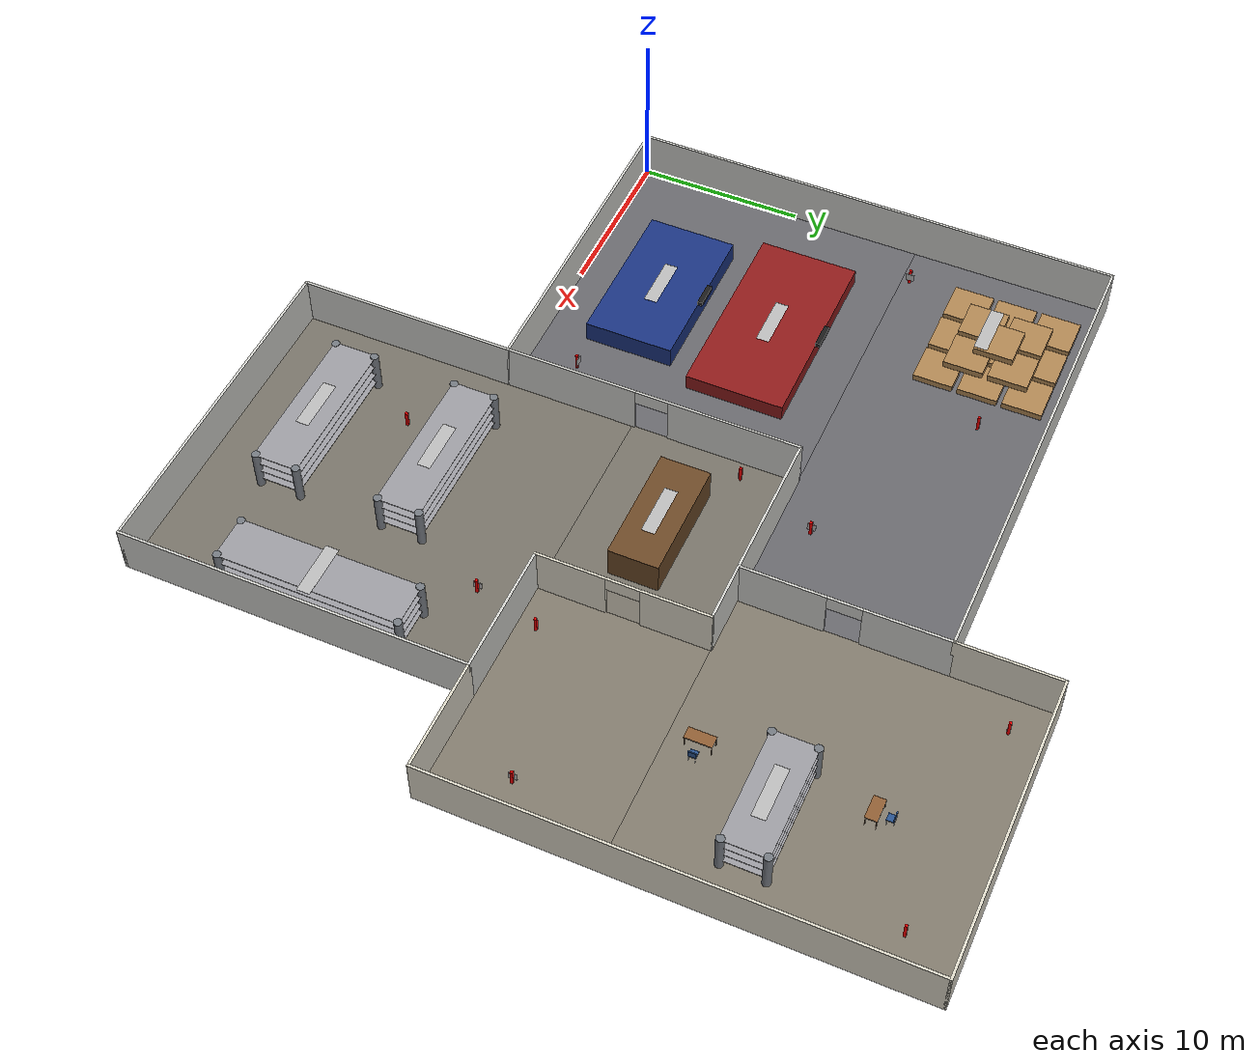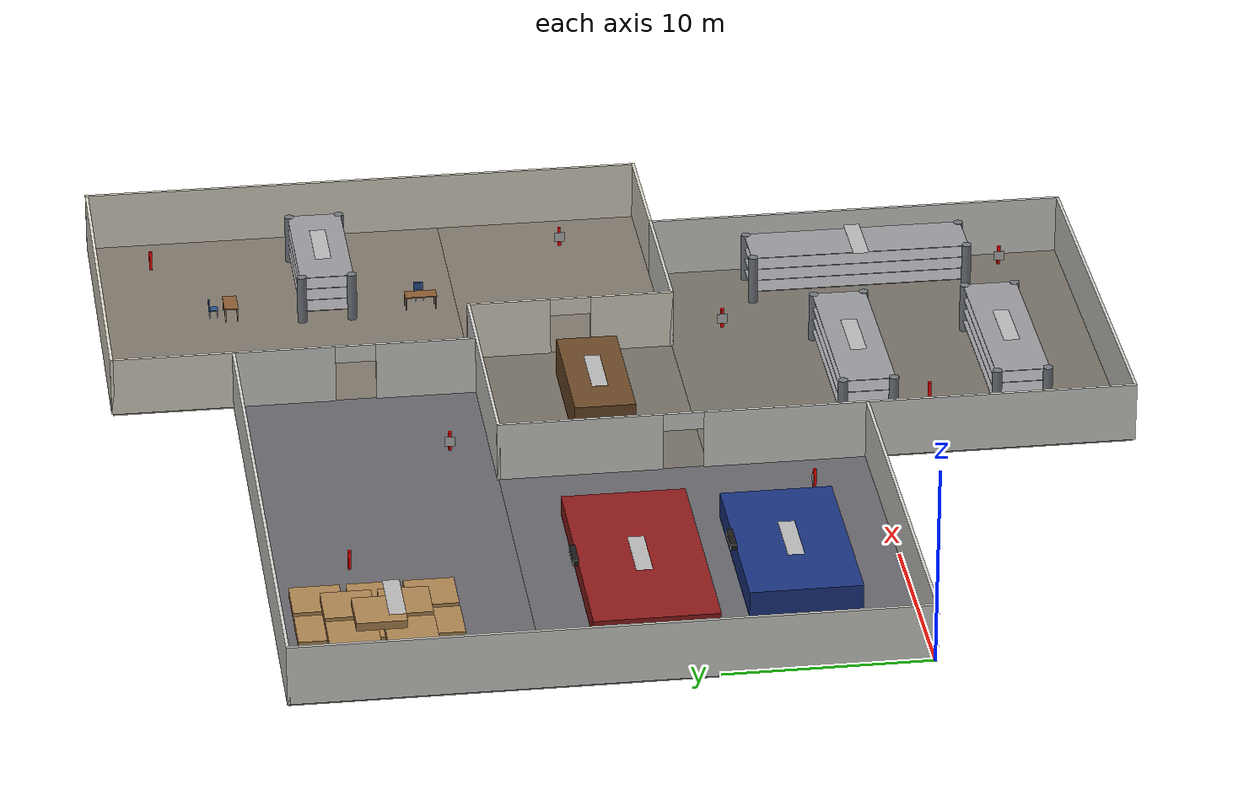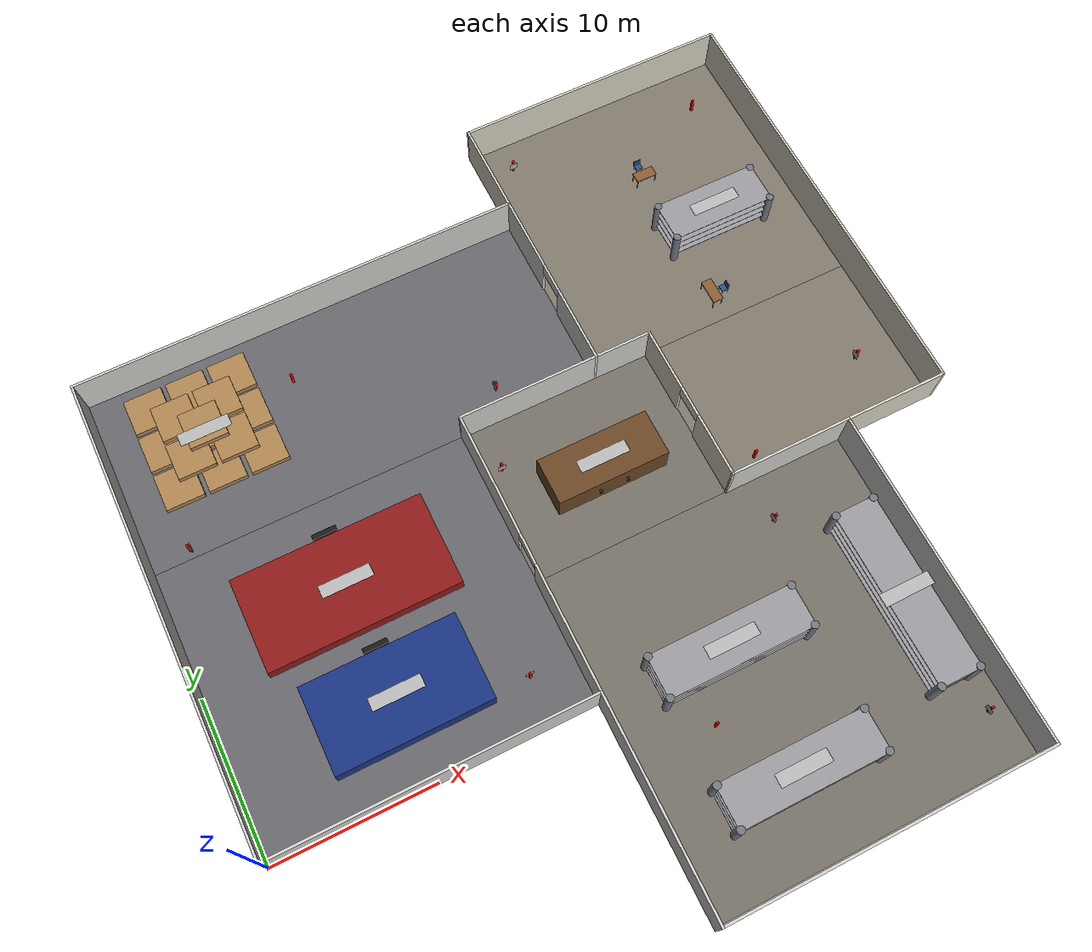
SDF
<sdf version="1.6">
 <world name="warehouse_world">
  <physics name="default_physics" default="true" type="ode">
   <max_step_size>0.001</max_step_size>
   <real_time_factor>1</real_time_factor>
   <real_time_update_rate>1000</real_time_update_rate>
   <ode>
    <solver><type>quick</type><iters>150</iters><sor>1.3</sor></solver>
    <constraints>
     <cfm>0.00001</cfm>
     <erp>0.2</erp>
     <contact_max_correcting_vel>100</contact_max_correcting_vel>
     <contact_surface_layer>0.001</contact_surface_layer>
    </constraints>
   </ode>
  </physics>
  <scene>
   <ambient>0.35 0.35 0.35 1</ambient>
   <background>0.55 0.62 0.7 1</background>
   <shadows>false</shadows>
   <grid>false</grid>
   <origin_visual>false</origin_visual>
  </scene>
  <light name="sun" type="directional">
   <pose>0 0 30 0 0 0</pose>
   <diffuse>0.85 0.85 0.82 1</diffuse>
   <specular>0.15 0.15 0.15 1</specular>
   <direction>-0.35 0.25 -0.9</direction>
  </light>
  <model name="wall_warehouse_west">
   <static>true</static>
   <pose>0.0000 15.0000 1.5000 0.0000 0.0000 0.0000</pose>
   <link name="link">
    <inertial>
     <mass>50.0</mass>
     <inertia><ixx>0.1</ixx><ixy>0</ixy><ixz>0</ixz><iyy>0.1</iyy><iyz>0</iyz><izz>0.1</izz></inertia>
    </inertial>
    <collision name="collision">
     <geometry><box><size>0.1500 30.1500 3.0000</size></box></geometry>
     <surface><friction><ode><mu>0.8</mu><mu2>0.8</mu2></ode></friction></surface>
    </collision>
    <visual name="visual">
     <geometry><box><size>0.1500 30.1500 3.0000</size></box></geometry>
     <material>
      <ambient>0.820 0.820 0.800 1.00</ambient>
      <diffuse>0.820 0.820 0.800 1.00</diffuse>
      <specular>0.15 0.15 0.15 1</specular>
      <emissive>0 0 0 1</emissive>
     </material>
    </visual>
   </link>
  </model>
  <model name="wall_warehouse_north">
   <static>true</static>
   <pose>14.4000 30.0000 1.5000 0.0000 0.0000 0.0000</pose>
   <link name="link">
    <inertial>
     <mass>50.0</mass>
     <inertia><ixx>0.1</ixx><ixy>0</ixy><ixz>0</ixz><iyy>0.1</iyy><iyz>0</iyz><izz>0.1</izz></inertia>
    </inertial>
    <collision name="collision">
     <geometry><box><size>28.9500 0.1500 3.0000</size></box></geometry>
     <surface><friction><ode><mu>0.8</mu><mu2>0.8</mu2></ode></friction></surface>
    </collision>
    <visual name="visual">
     <geometry><box><size>28.9500 0.1500 3.0000</size></box></geometry>
     <material>
      <ambient>0.820 0.820 0.800 1.00</ambient>
      <diffuse>0.820 0.820 0.800 1.00</diffuse>
      <specular>0.15 0.15 0.15 1</specular>
      <emissive>0 0 0 1</emissive>
     </material>
    </visual>
   </link>
  </model>
  <model name="wall_upper_storage_shared">
   <static>true</static>
   <pose>26.1000 18.0000 1.5000 0.0000 0.0000 0.0000</pose>
   <link name="link">
    <inertial>
     <mass>50.0</mass>
     <inertia><ixx>0.1</ixx><ixy>0</ixy><ixz>0</ixz><iyy>0.1</iyy><iyz>0</iyz><izz>0.1</izz></inertia>
    </inertial>
    <collision name="collision">
     <geometry><box><size>12.7500 0.1500 3.0000</size></box></geometry>
     <surface><friction><ode><mu>0.8</mu><mu2>0.8</mu2></ode></friction></surface>
    </collision>
    <visual name="visual">
     <geometry><box><size>12.7500 0.1500 3.0000</size></box></geometry>
     <material>
      <ambient>0.820 0.820 0.800 1.00</ambient>
      <diffuse>0.820 0.820 0.800 1.00</diffuse>
      <specular>0.15 0.15 0.15 1</specular>
      <emissive>0 0 0 1</emissive>
     </material>
    </visual>
   </link>
  </model>
  <model name="wall_storage_west_exterior">
   <static>true</static>
   <pose>19.8000 -6.6000 1.5000 0.0000 0.0000 0.0000</pose>
   <link name="link">
    <inertial>
     <mass>50.0</mass>
     <inertia><ixx>0.1</ixx><ixy>0</ixy><ixz>0</ixz><iyy>0.1</iyy><iyz>0</iyz><izz>0.1</izz></inertia>
    </inertial>
    <collision name="collision">
     <geometry><box><size>0.1500 13.3500 3.0000</size></box></geometry>
     <surface><friction><ode><mu>0.8</mu><mu2>0.8</mu2></ode></friction></surface>
    </collision>
    <visual name="visual">
     <geometry><box><size>0.1500 13.3500 3.0000</size></box></geometry>
     <material>
      <ambient>0.820 0.820 0.800 1.00</ambient>
      <diffuse>0.820 0.820 0.800 1.00</diffuse>
      <specular>0.15 0.15 0.15 1</specular>
      <emissive>0 0 0 1</emissive>
     </material>
    </visual>
   </link>
  </model>
  <model name="wall_warehouse_south">
   <static>true</static>
   <pose>9.9000 0.0000 1.5000 0.0000 0.0000 0.0000</pose>
   <link name="link">
    <inertial>
     <mass>50.0</mass>
     <inertia><ixx>0.1</ixx><ixy>0</ixy><ixz>0</ixz><iyy>0.1</iyy><iyz>0</iyz><izz>0.1</izz></inertia>
    </inertial>
    <collision name="collision">
     <geometry><box><size>19.9500 0.1500 3.0000</size></box></geometry>
     <surface><friction><ode><mu>0.8</mu><mu2>0.8</mu2></ode></friction></surface>
    </collision>
    <visual name="visual">
     <geometry><box><size>19.9500 0.1500 3.0000</size></box></geometry>
     <material>
      <ambient>0.820 0.820 0.800 1.00</ambient>
      <diffuse>0.820 0.820 0.800 1.00</diffuse>
      <specular>0.15 0.15 0.15 1</specular>
      <emissive>0 0 0 1</emissive>
     </material>
    </visual>
   </link>
  </model>
  <model name="wall_office_storage_shared_south">
   <static>true</static>
   <pose>36.3000 7.8000 1.5000 0.0000 0.0000 0.0000</pose>
   <link name="link">
    <inertial>
     <mass>50.0</mass>
     <inertia><ixx>0.1</ixx><ixy>0</ixy><ixz>0</ixz><iyy>0.1</iyy><iyz>0</iyz><izz>0.1</izz></inertia>
    </inertial>
    <collision name="collision">
     <geometry><box><size>7.9500 0.1500 3.0000</size></box></geometry>
     <surface><friction><ode><mu>0.8</mu><mu2>0.8</mu2></ode></friction></surface>
    </collision>
    <visual name="visual">
     <geometry><box><size>7.9500 0.1500 3.0000</size></box></geometry>
     <material>
      <ambient>0.820 0.820 0.800 1.00</ambient>
      <diffuse>0.820 0.820 0.800 1.00</diffuse>
      <specular>0.15 0.15 0.15 1</specular>
      <emissive>0 0 0 1</emissive>
     </material>
    </visual>
   </link>
  </model>
  <model name="wall_office_south_exterior">
   <static>true</static>
   <pose>43.5000 7.8000 1.5000 0.0000 0.0000 0.0000</pose>
   <link name="link">
    <inertial>
     <mass>50.0</mass>
     <inertia><ixx>0.1</ixx><ixy>0</ixy><ixz>0</ixz><iyy>0.1</iyy><iyz>0</iyz><izz>0.1</izz></inertia>
    </inertial>
    <collision name="collision">
     <geometry><box><size>6.7500 0.1500 3.0000</size></box></geometry>
     <surface><friction><ode><mu>0.8</mu><mu2>0.8</mu2></ode></friction></surface>
    </collision>
    <visual name="visual">
     <geometry><box><size>6.7500 0.1500 3.0000</size></box></geometry>
     <material>
      <ambient>0.860 0.840 0.780 1.00</ambient>
      <diffuse>0.860 0.840 0.780 1.00</diffuse>
      <specular>0.15 0.15 0.15 1</specular>
      <emissive>0 0 0 1</emissive>
     </material>
    </visual>
   </link>
  </model>
  <model name="wall_storage_east_exterior">
   <static>true</static>
   <pose>40.2000 -2.7000 1.5000 0.0000 0.0000 0.0000</pose>
   <link name="link">
    <inertial>
     <mass>50.0</mass>
     <inertia><ixx>0.1</ixx><ixy>0</ixy><ixz>0</ixz><iyy>0.1</iyy><iyz>0</iyz><izz>0.1</izz></inertia>
    </inertial>
    <collision name="collision">
     <geometry><box><size>0.1500 21.1500 3.0000</size></box></geometry>
     <surface><friction><ode><mu>0.8</mu><mu2>0.8</mu2></ode></friction></surface>
    </collision>
    <visual name="visual">
     <geometry><box><size>0.1500 21.1500 3.0000</size></box></geometry>
     <material>
      <ambient>0.820 0.820 0.800 1.00</ambient>
      <diffuse>0.820 0.820 0.800 1.00</diffuse>
      <specular>0.15 0.15 0.15 1</specular>
      <emissive>0 0 0 1</emissive>
     </material>
    </visual>
   </link>
  </model>
  <model name="wall_storage_south_exterior">
   <static>true</static>
   <pose>30.0000 -13.2000 1.5000 0.0000 0.0000 0.0000</pose>
   <link name="link">
    <inertial>
     <mass>50.0</mass>
     <inertia><ixx>0.1</ixx><ixy>0</ixy><ixz>0</ixz><iyy>0.1</iyy><iyz>0</iyz><izz>0.1</izz></inertia>
    </inertial>
    <collision name="collision">
     <geometry><box><size>20.5500 0.1500 3.0000</size></box></geometry>
     <surface><friction><ode><mu>0.8</mu><mu2>0.8</mu2></ode></friction></surface>
    </collision>
    <visual name="visual">
     <geometry><box><size>20.5500 0.1500 3.0000</size></box></geometry>
     <material>
      <ambient>0.820 0.820 0.800 1.00</ambient>
      <diffuse>0.820 0.820 0.800 1.00</diffuse>
      <specular>0.15 0.15 0.15 1</specular>
      <emissive>0 0 0 1</emissive>
     </material>
    </visual>
   </link>
  </model>
  <model name="wall_office_west_upper">
   <static>true</static>
   <pose>28.8000 33.0000 1.5000 0.0000 0.0000 0.0000</pose>
   <link name="link">
    <inertial>
     <mass>50.0</mass>
     <inertia><ixx>0.1</ixx><ixy>0</ixy><ixz>0</ixz><iyy>0.1</iyy><iyz>0</iyz><izz>0.1</izz></inertia>
    </inertial>
    <collision name="collision">
     <geometry><box><size>0.1500 6.1500 3.0000</size></box></geometry>
     <surface><friction><ode><mu>0.8</mu><mu2>0.8</mu2></ode></friction></surface>
    </collision>
    <visual name="visual">
     <geometry><box><size>0.1500 6.1500 3.0000</size></box></geometry>
     <material>
      <ambient>0.860 0.840 0.780 1.00</ambient>
      <diffuse>0.860 0.840 0.780 1.00</diffuse>
      <specular>0.15 0.15 0.15 1</specular>
      <emissive>0 0 0 1</emissive>
     </material>
    </visual>
   </link>
  </model>
  <model name="wall_office_north_exterior">
   <static>true</static>
   <pose>37.8000 36.0000 1.5000 0.0000 0.0000 0.0000</pose>
   <link name="link">
    <inertial>
     <mass>50.0</mass>
     <inertia><ixx>0.1</ixx><ixy>0</ixy><ixz>0</ixz><iyy>0.1</iyy><iyz>0</iyz><izz>0.1</izz></inertia>
    </inertial>
    <collision name="collision">
     <geometry><box><size>18.1500 0.1500 3.0000</size></box></geometry>
     <surface><friction><ode><mu>0.8</mu><mu2>0.8</mu2></ode></friction></surface>
    </collision>
    <visual name="visual">
     <geometry><box><size>18.1500 0.1500 3.0000</size></box></geometry>
     <material>
      <ambient>0.860 0.840 0.780 1.00</ambient>
      <diffuse>0.860 0.840 0.780 1.00</diffuse>
      <specular>0.15 0.15 0.15 1</specular>
      <emissive>0 0 0 1</emissive>
     </material>
    </visual>
   </link>
  </model>
  <model name="wall_office_east_exterior">
   <static>true</static>
   <pose>46.8000 21.9000 1.5000 0.0000 0.0000 0.0000</pose>
   <link name="link">
    <inertial>
     <mass>50.0</mass>
     <inertia><ixx>0.1</ixx><ixy>0</ixy><ixz>0</ixz><iyy>0.1</iyy><iyz>0</iyz><izz>0.1</izz></inertia>
    </inertial>
    <collision name="collision">
     <geometry><box><size>0.1500 28.3500 3.0000</size></box></geometry>
     <surface><friction><ode><mu>0.8</mu><mu2>0.8</mu2></ode></friction></surface>
    </collision>
    <visual name="visual">
     <geometry><box><size>0.1500 28.3500 3.0000</size></box></geometry>
     <material>
      <ambient>0.860 0.840 0.780 1.00</ambient>
      <diffuse>0.860 0.840 0.780 1.00</diffuse>
      <specular>0.15 0.15 0.15 1</specular>
      <emissive>0 0 0 1</emissive>
     </material>
    </visual>
   </link>
  </model>
  <model name="door_warehouse_office_jamb_a">
   <static>true</static>
   <pose>28.8000 20.4625 1.5000 0.0000 0.0000 0.0000</pose>
   <link name="link">
    <inertial>
     <mass>50.0</mass>
     <inertia><ixx>0.1</ixx><ixy>0</ixy><ixz>0</ixz><iyy>0.1</iyy><iyz>0</iyz><izz>0.1</izz></inertia>
    </inertial>
    <collision name="collision">
     <geometry><box><size>0.1500 5.0750 3.0000</size></box></geometry>
     <surface><friction><ode><mu>0.8</mu><mu2>0.8</mu2></ode></friction></surface>
    </collision>
    <visual name="visual">
     <geometry><box><size>0.1500 5.0750 3.0000</size></box></geometry>
     <material>
      <ambient>0.820 0.820 0.800 1.00</ambient>
      <diffuse>0.820 0.820 0.800 1.00</diffuse>
      <specular>0.15 0.15 0.15 1</specular>
      <emissive>0 0 0 1</emissive>
     </material>
    </visual>
   </link>
  </model>
  <model name="door_warehouse_office_jamb_b">
   <static>true</static>
   <pose>28.8000 27.5375 1.5000 0.0000 0.0000 0.0000</pose>
   <link name="link">
    <inertial>
     <mass>50.0</mass>
     <inertia><ixx>0.1</ixx><ixy>0</ixy><ixz>0</ixz><iyy>0.1</iyy><iyz>0</iyz><izz>0.1</izz></inertia>
    </inertial>
    <collision name="collision">
     <geometry><box><size>0.1500 5.0750 3.0000</size></box></geometry>
     <surface><friction><ode><mu>0.8</mu><mu2>0.8</mu2></ode></friction></surface>
    </collision>
    <visual name="visual">
     <geometry><box><size>0.1500 5.0750 3.0000</size></box></geometry>
     <material>
      <ambient>0.820 0.820 0.800 1.00</ambient>
      <diffuse>0.820 0.820 0.800 1.00</diffuse>
      <specular>0.15 0.15 0.15 1</specular>
      <emissive>0 0 0 1</emissive>
     </material>
    </visual>
   </link>
  </model>
  <model name="door_warehouse_office_header">
   <static>true</static>
   <pose>28.8000 24.0000 2.5500 0.0000 0.0000 0.0000</pose>
   <link name="link">
    <inertial>
     <mass>10.0</mass>
     <inertia><ixx>0.1</ixx><ixy>0</ixy><ixz>0</ixz><iyy>0.1</iyy><iyz>0</iyz><izz>0.1</izz></inertia>
    </inertial>
    <collision name="collision">
     <geometry><box><size>0.1500 2.0000 0.9000</size></box></geometry>
     <surface><friction><ode><mu>0.8</mu><mu2>0.8</mu2></ode></friction></surface>
    </collision>
    <visual name="visual">
     <geometry><box><size>0.1500 2.0000 0.9000</size></box></geometry>
     <material>
      <ambient>0.820 0.820 0.800 1.00</ambient>
      <diffuse>0.820 0.820 0.800 1.00</diffuse>
      <specular>0.15 0.15 0.15 1</specular>
      <emissive>0 0 0 1</emissive>
     </material>
    </visual>
   </link>
  </model>
  <model name="door_warehouse_storage_jamb_a">
   <static>true</static>
   <pose>19.8000 3.9625 1.5000 0.0000 0.0000 0.0000</pose>
   <link name="link">
    <inertial>
     <mass>50.0</mass>
     <inertia><ixx>0.1</ixx><ixy>0</ixy><ixz>0</ixz><iyy>0.1</iyy><iyz>0</iyz><izz>0.1</izz></inertia>
    </inertial>
    <collision name="collision">
     <geometry><box><size>0.1500 8.0750 3.0000</size></box></geometry>
     <surface><friction><ode><mu>0.8</mu><mu2>0.8</mu2></ode></friction></surface>
    </collision>
    <visual name="visual">
     <geometry><box><size>0.1500 8.0750 3.0000</size></box></geometry>
     <material>
      <ambient>0.820 0.820 0.800 1.00</ambient>
      <diffuse>0.820 0.820 0.800 1.00</diffuse>
      <specular>0.15 0.15 0.15 1</specular>
      <emissive>0 0 0 1</emissive>
     </material>
    </visual>
   </link>
  </model>
  <model name="door_warehouse_storage_jamb_b">
   <static>true</static>
   <pose>19.8000 14.0375 1.5000 0.0000 0.0000 0.0000</pose>
   <link name="link">
    <inertial>
     <mass>50.0</mass>
     <inertia><ixx>0.1</ixx><ixy>0</ixy><ixz>0</ixz><iyy>0.1</iyy><iyz>0</iyz><izz>0.1</izz></inertia>
    </inertial>
    <collision name="collision">
     <geometry><box><size>0.1500 8.0750 3.0000</size></box></geometry>
     <surface><friction><ode><mu>0.8</mu><mu2>0.8</mu2></ode></friction></surface>
    </collision>
    <visual name="visual">
     <geometry><box><size>0.1500 8.0750 3.0000</size></box></geometry>
     <material>
      <ambient>0.820 0.820 0.800 1.00</ambient>
      <diffuse>0.820 0.820 0.800 1.00</diffuse>
      <specular>0.15 0.15 0.15 1</specular>
      <emissive>0 0 0 1</emissive>
     </material>
    </visual>
   </link>
  </model>
  <model name="door_warehouse_storage_header">
   <static>true</static>
   <pose>19.8000 9.0000 2.5500 0.0000 0.0000 0.0000</pose>
   <link name="link">
    <inertial>
     <mass>10.0</mass>
     <inertia><ixx>0.1</ixx><ixy>0</ixy><ixz>0</ixz><iyy>0.1</iyy><iyz>0</iyz><izz>0.1</izz></inertia>
    </inertial>
    <collision name="collision">
     <geometry><box><size>0.1500 2.0000 0.9000</size></box></geometry>
     <surface><friction><ode><mu>0.8</mu><mu2>0.8</mu2></ode></friction></surface>
    </collision>
    <visual name="visual">
     <geometry><box><size>0.1500 2.0000 0.9000</size></box></geometry>
     <material>
      <ambient>0.820 0.820 0.800 1.00</ambient>
      <diffuse>0.820 0.820 0.800 1.00</diffuse>
      <specular>0.15 0.15 0.15 1</specular>
      <emissive>0 0 0 1</emissive>
     </material>
    </visual>
   </link>
  </model>
  <model name="door_office_storage_jamb_a">
   <static>true</static>
   <pose>32.4000 9.8125 1.5000 0.0000 0.0000 0.0000</pose>
   <link name="link">
    <inertial>
     <mass>50.0</mass>
     <inertia><ixx>0.1</ixx><ixy>0</ixy><ixz>0</ixz><iyy>0.1</iyy><iyz>0</iyz><izz>0.1</izz></inertia>
    </inertial>
    <collision name="collision">
     <geometry><box><size>0.1500 4.1750 3.0000</size></box></geometry>
     <surface><friction><ode><mu>0.8</mu><mu2>0.8</mu2></ode></friction></surface>
    </collision>
    <visual name="visual">
     <geometry><box><size>0.1500 4.1750 3.0000</size></box></geometry>
     <material>
      <ambient>0.860 0.840 0.780 1.00</ambient>
      <diffuse>0.860 0.840 0.780 1.00</diffuse>
      <specular>0.15 0.15 0.15 1</specular>
      <emissive>0 0 0 1</emissive>
     </material>
    </visual>
   </link>
  </model>
  <model name="door_office_storage_jamb_b">
   <static>true</static>
   <pose>32.4000 15.9875 1.5000 0.0000 0.0000 0.0000</pose>
   <link name="link">
    <inertial>
     <mass>50.0</mass>
     <inertia><ixx>0.1</ixx><ixy>0</ixy><ixz>0</ixz><iyy>0.1</iyy><iyz>0</iyz><izz>0.1</izz></inertia>
    </inertial>
    <collision name="collision">
     <geometry><box><size>0.1500 4.1750 3.0000</size></box></geometry>
     <surface><friction><ode><mu>0.8</mu><mu2>0.8</mu2></ode></friction></surface>
    </collision>
    <visual name="visual">
     <geometry><box><size>0.1500 4.1750 3.0000</size></box></geometry>
     <material>
      <ambient>0.860 0.840 0.780 1.00</ambient>
      <diffuse>0.860 0.840 0.780 1.00</diffuse>
      <specular>0.15 0.15 0.15 1</specular>
      <emissive>0 0 0 1</emissive>
     </material>
    </visual>
   </link>
  </model>
  <model name="door_office_storage_header">
   <static>true</static>
   <pose>32.4000 12.9000 2.5500 0.0000 0.0000 0.0000</pose>
   <link name="link">
    <inertial>
     <mass>10.0</mass>
     <inertia><ixx>0.1</ixx><ixy>0</ixy><ixz>0</ixz><iyy>0.1</iyy><iyz>0</iyz><izz>0.1</izz></inertia>
    </inertial>
    <collision name="collision">
     <geometry><box><size>0.1500 2.0000 0.9000</size></box></geometry>
     <surface><friction><ode><mu>0.8</mu><mu2>0.8</mu2></ode></friction></surface>
    </collision>
    <visual name="visual">
     <geometry><box><size>0.1500 2.0000 0.9000</size></box></geometry>
     <material>
      <ambient>0.860 0.840 0.780 1.00</ambient>
      <diffuse>0.860 0.840 0.780 1.00</diffuse>
      <specular>0.15 0.15 0.15 1</specular>
      <emissive>0 0 0 1</emissive>
     </material>
    </visual>
   </link>
  </model>
  <model name="floor_warehouse_upper">
   <static>true</static>
   <pose>14.4000 24.0000 -0.0500 0.0000 0.0000 0.0000</pose>
   <link name="link">
    <inertial>
     <mass>100.0</mass>
     <inertia><ixx>0.1</ixx><ixy>0</ixy><ixz>0</ixz><iyy>0.1</iyy><iyz>0</iyz><izz>0.1</izz></inertia>
    </inertial>
    <collision name="collision">
     <geometry><box><size>28.8000 12.0000 0.1000</size></box></geometry>
     <surface><friction><ode><mu>0.8</mu><mu2>0.8</mu2></ode></friction></surface>
    </collision>
    <visual name="visual">
     <geometry><box><size>28.8000 12.0000 0.1000</size></box></geometry>
     <material>
      <ambient>0.400 0.400 0.420 1.00</ambient>
      <diffuse>0.400 0.400 0.420 1.00</diffuse>
      <specular>0.15 0.15 0.15 1</specular>
      <emissive>0 0 0 1</emissive>
     </material>
    </visual>
   </link>
  </model>
  <model name="floor_warehouse_lower">
   <static>true</static>
   <pose>9.9000 9.0000 -0.0500 0.0000 0.0000 0.0000</pose>
   <link name="link">
    <inertial>
     <mass>100.0</mass>
     <inertia><ixx>0.1</ixx><ixy>0</ixy><ixz>0</ixz><iyy>0.1</iyy><iyz>0</iyz><izz>0.1</izz></inertia>
    </inertial>
    <collision name="collision">
     <geometry><box><size>19.8000 18.0000 0.1000</size></box></geometry>
     <surface><friction><ode><mu>0.8</mu><mu2>0.8</mu2></ode></friction></surface>
    </collision>
    <visual name="visual">
     <geometry><box><size>19.8000 18.0000 0.1000</size></box></geometry>
     <material>
      <ambient>0.400 0.400 0.420 1.00</ambient>
      <diffuse>0.400 0.400 0.420 1.00</diffuse>
      <specular>0.15 0.15 0.15 1</specular>
      <emissive>0 0 0 1</emissive>
     </material>
    </visual>
   </link>
  </model>
  <model name="floor_storage_upper">
   <static>true</static>
   <pose>26.1000 12.9000 -0.0500 0.0000 0.0000 0.0000</pose>
   <link name="link">
    <inertial>
     <mass>100.0</mass>
     <inertia><ixx>0.1</ixx><ixy>0</ixy><ixz>0</ixz><iyy>0.1</iyy><iyz>0</iyz><izz>0.1</izz></inertia>
    </inertial>
    <collision name="collision">
     <geometry><box><size>12.6000 10.2000 0.1000</size></box></geometry>
     <surface><friction><ode><mu>0.8</mu><mu2>0.8</mu2></ode></friction></surface>
    </collision>
    <visual name="visual">
     <geometry><box><size>12.6000 10.2000 0.1000</size></box></geometry>
     <material>
      <ambient>0.460 0.440 0.400 1.00</ambient>
      <diffuse>0.460 0.440 0.400 1.00</diffuse>
      <specular>0.15 0.15 0.15 1</specular>
      <emissive>0 0 0 1</emissive>
     </material>
    </visual>
   </link>
  </model>
  <model name="floor_storage_lower">
   <static>true</static>
   <pose>30.0000 -2.7000 -0.0500 0.0000 0.0000 0.0000</pose>
   <link name="link">
    <inertial>
     <mass>100.0</mass>
     <inertia><ixx>0.1</ixx><ixy>0</ixy><ixz>0</ixz><iyy>0.1</iyy><iyz>0</iyz><izz>0.1</izz></inertia>
    </inertial>
    <collision name="collision">
     <geometry><box><size>20.4000 21.0000 0.1000</size></box></geometry>
     <surface><friction><ode><mu>0.8</mu><mu2>0.8</mu2></ode></friction></surface>
    </collision>
    <visual name="visual">
     <geometry><box><size>20.4000 21.0000 0.1000</size></box></geometry>
     <material>
      <ambient>0.460 0.440 0.400 1.00</ambient>
      <diffuse>0.460 0.440 0.400 1.00</diffuse>
      <specular>0.15 0.15 0.15 1</specular>
      <emissive>0 0 0 1</emissive>
     </material>
    </visual>
   </link>
  </model>
  <model name="floor_office_upper">
   <static>true</static>
   <pose>37.8000 27.0000 -0.0500 0.0000 0.0000 0.0000</pose>
   <link name="link">
    <inertial>
     <mass>100.0</mass>
     <inertia><ixx>0.1</ixx><ixy>0</ixy><ixz>0</ixz><iyy>0.1</iyy><iyz>0</iyz><izz>0.1</izz></inertia>
    </inertial>
    <collision name="collision">
     <geometry><box><size>18.0000 18.0000 0.1000</size></box></geometry>
     <surface><friction><ode><mu>0.8</mu><mu2>0.8</mu2></ode></friction></surface>
    </collision>
    <visual name="visual">
     <geometry><box><size>18.0000 18.0000 0.1000</size></box></geometry>
     <material>
      <ambient>0.500 0.470 0.420 1.00</ambient>
      <diffuse>0.500 0.470 0.420 1.00</diffuse>
      <specular>0.15 0.15 0.15 1</specular>
      <emissive>0 0 0 1</emissive>
     </material>
    </visual>
   </link>
  </model>
  <model name="floor_office_lower">
   <static>true</static>
   <pose>39.6000 12.9000 -0.0500 0.0000 0.0000 0.0000</pose>
   <link name="link">
    <inertial>
     <mass>100.0</mass>
     <inertia><ixx>0.1</ixx><ixy>0</ixy><ixz>0</ixz><iyy>0.1</iyy><iyz>0</iyz><izz>0.1</izz></inertia>
    </inertial>
    <collision name="collision">
     <geometry><box><size>14.4000 10.2000 0.1000</size></box></geometry>
     <surface><friction><ode><mu>0.8</mu><mu2>0.8</mu2></ode></friction></surface>
    </collision>
    <visual name="visual">
     <geometry><box><size>14.4000 10.2000 0.1000</size></box></geometry>
     <material>
      <ambient>0.500 0.470 0.420 1.00</ambient>
      <diffuse>0.500 0.470 0.420 1.00</diffuse>
      <specular>0.15 0.15 0.15 1</specular>
      <emissive>0 0 0 1</emissive>
     </material>
    </visual>
   </link>
  </model>
  <model name="loading_area_pad">
   <static>true</static>
   <pose>6.0000 25.2000 0.0010 0.0000 0.0000 0.0000</pose>
   <link name="link">
    <inertial>
     <mass>5.0</mass>
     <inertia><ixx>0.1</ixx><ixy>0</ixy><ixz>0</ixz><iyy>0.1</iyy><iyz>0</iyz><izz>0.1</izz></inertia>
    </inertial>
    <collision name="collision">
     <geometry><plane><normal>0 0 1</normal><size>9.6000 9.6000</size></plane></geometry>
     <surface><friction><ode><mu>0.8</mu><mu2>0.8</mu2></ode></friction></surface>
    </collision>
    <visual name="visual">
     <geometry><plane><normal>0 0 1</normal><size>9.6000 9.6000</size></plane></geometry>
     <material>
      <ambient>0.850 0.700 0.100 1.00</ambient>
      <diffuse>0.850 0.700 0.100 1.00</diffuse>
      <specular>0.15 0.15 0.15 1</specular>
      <emissive>0 0 0 1</emissive>
     </material>
    </visual>
   </link>
  </model>
  <model name="loading_box_base_1">
   <static>true</static>
   <pose>3.3000 22.5000 0.2000 0.0000 0.0000 0.0000</pose>
   <link name="link">
    <inertial>
     <mass>8.0</mass>
     <inertia><ixx>0.1</ixx><ixy>0</ixy><ixz>0</ixz><iyy>0.1</iyy><iyz>0</iyz><izz>0.1</izz></inertia>
    </inertial>
    <collision name="collision">
     <geometry><box><size>2.4000 2.4000 0.4000</size></box></geometry>
     <surface><friction><ode><mu>0.8</mu><mu2>0.8</mu2></ode></friction></surface>
    </collision>
    <visual name="visual">
     <geometry><box><size>2.4000 2.4000 0.4000</size></box></geometry>
     <material>
      <ambient>0.680 0.520 0.320 1.00</ambient>
      <diffuse>0.680 0.520 0.320 1.00</diffuse>
      <specular>0.15 0.15 0.15 1</specular>
      <emissive>0 0 0 1</emissive>
     </material>
    </visual>
   </link>
  </model>
  <model name="loading_box_base_2">
   <static>true</static>
   <pose>6.0000 22.5000 0.2000 0.0000 0.0000 0.0000</pose>
   <link name="link">
    <inertial>
     <mass>8.0</mass>
     <inertia><ixx>0.1</ixx><ixy>0</ixy><ixz>0</ixz><iyy>0.1</iyy><iyz>0</iyz><izz>0.1</izz></inertia>
    </inertial>
    <collision name="collision">
     <geometry><box><size>2.4000 2.4000 0.4000</size></box></geometry>
     <surface><friction><ode><mu>0.8</mu><mu2>0.8</mu2></ode></friction></surface>
    </collision>
    <visual name="visual">
     <geometry><box><size>2.4000 2.4000 0.4000</size></box></geometry>
     <material>
      <ambient>0.680 0.520 0.320 1.00</ambient>
      <diffuse>0.680 0.520 0.320 1.00</diffuse>
      <specular>0.15 0.15 0.15 1</specular>
      <emissive>0 0 0 1</emissive>
     </material>
    </visual>
   </link>
  </model>
  <model name="loading_box_base_3">
   <static>true</static>
   <pose>8.7000 22.5000 0.2000 0.0000 0.0000 0.0000</pose>
   <link name="link">
    <inertial>
     <mass>8.0</mass>
     <inertia><ixx>0.1</ixx><ixy>0</ixy><ixz>0</ixz><iyy>0.1</iyy><iyz>0</iyz><izz>0.1</izz></inertia>
    </inertial>
    <collision name="collision">
     <geometry><box><size>2.4000 2.4000 0.4000</size></box></geometry>
     <surface><friction><ode><mu>0.8</mu><mu2>0.8</mu2></ode></friction></surface>
    </collision>
    <visual name="visual">
     <geometry><box><size>2.4000 2.4000 0.4000</size></box></geometry>
     <material>
      <ambient>0.680 0.520 0.320 1.00</ambient>
      <diffuse>0.680 0.520 0.320 1.00</diffuse>
      <specular>0.15 0.15 0.15 1</specular>
      <emissive>0 0 0 1</emissive>
     </material>
    </visual>
   </link>
  </model>
  <model name="loading_box_base_4">
   <static>true</static>
   <pose>3.3000 25.2000 0.2000 0.0000 0.0000 0.0000</pose>
   <link name="link">
    <inertial>
     <mass>8.0</mass>
     <inertia><ixx>0.1</ixx><ixy>0</ixy><ixz>0</ixz><iyy>0.1</iyy><iyz>0</iyz><izz>0.1</izz></inertia>
    </inertial>
    <collision name="collision">
     <geometry><box><size>2.4000 2.4000 0.4000</size></box></geometry>
     <surface><friction><ode><mu>0.8</mu><mu2>0.8</mu2></ode></friction></surface>
    </collision>
    <visual name="visual">
     <geometry><box><size>2.4000 2.4000 0.4000</size></box></geometry>
     <material>
      <ambient>0.680 0.520 0.320 1.00</ambient>
      <diffuse>0.680 0.520 0.320 1.00</diffuse>
      <specular>0.15 0.15 0.15 1</specular>
      <emissive>0 0 0 1</emissive>
     </material>
    </visual>
   </link>
  </model>
  <model name="loading_box_base_5">
   <static>true</static>
   <pose>6.0000 25.2000 0.2000 0.0000 0.0000 0.0000</pose>
   <link name="link">
    <inertial>
     <mass>8.0</mass>
     <inertia><ixx>0.1</ixx><ixy>0</ixy><ixz>0</ixz><iyy>0.1</iyy><iyz>0</iyz><izz>0.1</izz></inertia>
    </inertial>
    <collision name="collision">
     <geometry><box><size>2.4000 2.4000 0.4000</size></box></geometry>
     <surface><friction><ode><mu>0.8</mu><mu2>0.8</mu2></ode></friction></surface>
    </collision>
    <visual name="visual">
     <geometry><box><size>2.4000 2.4000 0.4000</size></box></geometry>
     <material>
      <ambient>0.680 0.520 0.320 1.00</ambient>
      <diffuse>0.680 0.520 0.320 1.00</diffuse>
      <specular>0.15 0.15 0.15 1</specular>
      <emissive>0 0 0 1</emissive>
     </material>
    </visual>
   </link>
  </model>
  <model name="loading_box_base_6">
   <static>true</static>
   <pose>8.7000 25.2000 0.2000 0.0000 0.0000 0.0000</pose>
   <link name="link">
    <inertial>
     <mass>8.0</mass>
     <inertia><ixx>0.1</ixx><ixy>0</ixy><ixz>0</ixz><iyy>0.1</iyy><iyz>0</iyz><izz>0.1</izz></inertia>
    </inertial>
    <collision name="collision">
     <geometry><box><size>2.4000 2.4000 0.4000</size></box></geometry>
     <surface><friction><ode><mu>0.8</mu><mu2>0.8</mu2></ode></friction></surface>
    </collision>
    <visual name="visual">
     <geometry><box><size>2.4000 2.4000 0.4000</size></box></geometry>
     <material>
      <ambient>0.680 0.520 0.320 1.00</ambient>
      <diffuse>0.680 0.520 0.320 1.00</diffuse>
      <specular>0.15 0.15 0.15 1</specular>
      <emissive>0 0 0 1</emissive>
     </material>
    </visual>
   </link>
  </model>
  <model name="loading_box_base_7">
   <static>true</static>
   <pose>3.3000 27.9000 0.2000 0.0000 0.0000 0.0000</pose>
   <link name="link">
    <inertial>
     <mass>8.0</mass>
     <inertia><ixx>0.1</ixx><ixy>0</ixy><ixz>0</ixz><iyy>0.1</iyy><iyz>0</iyz><izz>0.1</izz></inertia>
    </inertial>
    <collision name="collision">
     <geometry><box><size>2.4000 2.4000 0.4000</size></box></geometry>
     <surface><friction><ode><mu>0.8</mu><mu2>0.8</mu2></ode></friction></surface>
    </collision>
    <visual name="visual">
     <geometry><box><size>2.4000 2.4000 0.4000</size></box></geometry>
     <material>
      <ambient>0.680 0.520 0.320 1.00</ambient>
      <diffuse>0.680 0.520 0.320 1.00</diffuse>
      <specular>0.15 0.15 0.15 1</specular>
      <emissive>0 0 0 1</emissive>
     </material>
    </visual>
   </link>
  </model>
  <model name="loading_box_base_8">
   <static>true</static>
   <pose>6.0000 27.9000 0.2000 0.0000 0.0000 0.0000</pose>
   <link name="link">
    <inertial>
     <mass>8.0</mass>
     <inertia><ixx>0.1</ixx><ixy>0</ixy><ixz>0</ixz><iyy>0.1</iyy><iyz>0</iyz><izz>0.1</izz></inertia>
    </inertial>
    <collision name="collision">
     <geometry><box><size>2.4000 2.4000 0.4000</size></box></geometry>
     <surface><friction><ode><mu>0.8</mu><mu2>0.8</mu2></ode></friction></surface>
    </collision>
    <visual name="visual">
     <geometry><box><size>2.4000 2.4000 0.4000</size></box></geometry>
     <material>
      <ambient>0.680 0.520 0.320 1.00</ambient>
      <diffuse>0.680 0.520 0.320 1.00</diffuse>
      <specular>0.15 0.15 0.15 1</specular>
      <emissive>0 0 0 1</emissive>
     </material>
    </visual>
   </link>
  </model>
  <model name="loading_box_base_9">
   <static>true</static>
   <pose>8.7000 27.9000 0.2000 0.0000 0.0000 0.0000</pose>
   <link name="link">
    <inertial>
     <mass>8.0</mass>
     <inertia><ixx>0.1</ixx><ixy>0</ixy><ixz>0</ixz><iyy>0.1</iyy><iyz>0</iyz><izz>0.1</izz></inertia>
    </inertial>
    <collision name="collision">
     <geometry><box><size>2.4000 2.4000 0.4000</size></box></geometry>
     <surface><friction><ode><mu>0.8</mu><mu2>0.8</mu2></ode></friction></surface>
    </collision>
    <visual name="visual">
     <geometry><box><size>2.4000 2.4000 0.4000</size></box></geometry>
     <material>
      <ambient>0.680 0.520 0.320 1.00</ambient>
      <diffuse>0.680 0.520 0.320 1.00</diffuse>
      <specular>0.15 0.15 0.15 1</specular>
      <emissive>0 0 0 1</emissive>
     </material>
    </visual>
   </link>
  </model>
  <model name="loading_box_mid_1">
   <static>true</static>
   <pose>4.6500 23.8500 0.6000 0.0000 0.0000 0.0000</pose>
   <link name="link">
    <inertial>
     <mass>8.0</mass>
     <inertia><ixx>0.1</ixx><ixy>0</ixy><ixz>0</ixz><iyy>0.1</iyy><iyz>0</iyz><izz>0.1</izz></inertia>
    </inertial>
    <collision name="collision">
     <geometry><box><size>2.4000 2.4000 0.4000</size></box></geometry>
     <surface><friction><ode><mu>0.8</mu><mu2>0.8</mu2></ode></friction></surface>
    </collision>
    <visual name="visual">
     <geometry><box><size>2.4000 2.4000 0.4000</size></box></geometry>
     <material>
      <ambient>0.680 0.520 0.320 1.00</ambient>
      <diffuse>0.680 0.520 0.320 1.00</diffuse>
      <specular>0.15 0.15 0.15 1</specular>
      <emissive>0 0 0 1</emissive>
     </material>
    </visual>
   </link>
  </model>
  <model name="loading_box_mid_2">
   <static>true</static>
   <pose>7.3500 23.8500 0.6000 0.0000 0.0000 0.0000</pose>
   <link name="link">
    <inertial>
     <mass>8.0</mass>
     <inertia><ixx>0.1</ixx><ixy>0</ixy><ixz>0</ixz><iyy>0.1</iyy><iyz>0</iyz><izz>0.1</izz></inertia>
    </inertial>
    <collision name="collision">
     <geometry><box><size>2.4000 2.4000 0.4000</size></box></geometry>
     <surface><friction><ode><mu>0.8</mu><mu2>0.8</mu2></ode></friction></surface>
    </collision>
    <visual name="visual">
     <geometry><box><size>2.4000 2.4000 0.4000</size></box></geometry>
     <material>
      <ambient>0.680 0.520 0.320 1.00</ambient>
      <diffuse>0.680 0.520 0.320 1.00</diffuse>
      <specular>0.15 0.15 0.15 1</specular>
      <emissive>0 0 0 1</emissive>
     </material>
    </visual>
   </link>
  </model>
  <model name="loading_box_mid_3">
   <static>true</static>
   <pose>4.6500 26.5500 0.6000 0.0000 0.0000 0.0000</pose>
   <link name="link">
    <inertial>
     <mass>8.0</mass>
     <inertia><ixx>0.1</ixx><ixy>0</ixy><ixz>0</ixz><iyy>0.1</iyy><iyz>0</iyz><izz>0.1</izz></inertia>
    </inertial>
    <collision name="collision">
     <geometry><box><size>2.4000 2.4000 0.4000</size></box></geometry>
     <surface><friction><ode><mu>0.8</mu><mu2>0.8</mu2></ode></friction></surface>
    </collision>
    <visual name="visual">
     <geometry><box><size>2.4000 2.4000 0.4000</size></box></geometry>
     <material>
      <ambient>0.680 0.520 0.320 1.00</ambient>
      <diffuse>0.680 0.520 0.320 1.00</diffuse>
      <specular>0.15 0.15 0.15 1</specular>
      <emissive>0 0 0 1</emissive>
     </material>
    </visual>
   </link>
  </model>
  <model name="loading_box_mid_4">
   <static>true</static>
   <pose>7.3500 26.5500 0.6000 0.0000 0.0000 0.0000</pose>
   <link name="link">
    <inertial>
     <mass>8.0</mass>
     <inertia><ixx>0.1</ixx><ixy>0</ixy><ixz>0</ixz><iyy>0.1</iyy><iyz>0</iyz><izz>0.1</izz></inertia>
    </inertial>
    <collision name="collision">
     <geometry><box><size>2.4000 2.4000 0.4000</size></box></geometry>
     <surface><friction><ode><mu>0.8</mu><mu2>0.8</mu2></ode></friction></surface>
    </collision>
    <visual name="visual">
     <geometry><box><size>2.4000 2.4000 0.4000</size></box></geometry>
     <material>
      <ambient>0.680 0.520 0.320 1.00</ambient>
      <diffuse>0.680 0.520 0.320 1.00</diffuse>
      <specular>0.15 0.15 0.15 1</specular>
      <emissive>0 0 0 1</emissive>
     </material>
    </visual>
   </link>
  </model>
  <model name="loading_box_top_1">
   <static>true</static>
   <pose>6.0000 25.2000 1.0000 0.0000 0.0000 0.0000</pose>
   <link name="link">
    <inertial>
     <mass>8.0</mass>
     <inertia><ixx>0.1</ixx><ixy>0</ixy><ixz>0</ixz><iyy>0.1</iyy><iyz>0</iyz><izz>0.1</izz></inertia>
    </inertial>
    <collision name="collision">
     <geometry><box><size>2.4000 2.4000 0.4000</size></box></geometry>
     <surface><friction><ode><mu>0.8</mu><mu2>0.8</mu2></ode></friction></surface>
    </collision>
    <visual name="visual">
     <geometry><box><size>2.4000 2.4000 0.4000</size></box></geometry>
     <material>
      <ambient>0.680 0.520 0.320 1.00</ambient>
      <diffuse>0.680 0.520 0.320 1.00</diffuse>
      <specular>0.15 0.15 0.15 1</specular>
      <emissive>0 0 0 1</emissive>
     </material>
    </visual>
   </link>
  </model>
  <model name="machine_1">
   <static>true</static>
   <pose>9.9000 12.4500 0.5000 0.0000 0.0000 0.0000</pose>
   <link name="link">
    <inertial>
     <mass>250.0</mass>
     <inertia><ixx>0.1</ixx><ixy>0</ixy><ixz>0</ixz><iyy>0.1</iyy><iyz>0</iyz><izz>0.1</izz></inertia>
    </inertial>
    <collision name="collision">
     <geometry><box><size>12.0000 6.0000 1.0000</size></box></geometry>
     <surface><friction><ode><mu>0.8</mu><mu2>0.8</mu2></ode></friction></surface>
    </collision>
    <visual name="visual">
     <geometry><box><size>12.0000 6.0000 1.0000</size></box></geometry>
     <material>
      <ambient>0.550 0.100 0.100 1.00</ambient>
      <diffuse>0.550 0.100 0.100 1.00</diffuse>
      <specular>0.15 0.15 0.15 1</specular>
      <emissive>0 0 0 1</emissive>
     </material>
    </visual>
   </link>
  </model>
  <model name="machine_1_panel">
   <static>true</static>
   <pose>9.9000 15.6000 1.1500 0.0000 0.0000 0.0000</pose>
   <link name="link">
    <inertial>
     <mass>2.0</mass>
     <inertia><ixx>0.1</ixx><ixy>0</ixy><ixz>0</ixz><iyy>0.1</iyy><iyz>0</iyz><izz>0.1</izz></inertia>
    </inertial>
    <collision name="collision">
     <geometry><box><size>1.5000 0.3000 0.3000</size></box></geometry>
     <surface><friction><ode><mu>0.8</mu><mu2>0.8</mu2></ode></friction></surface>
    </collision>
    <visual name="visual">
     <geometry><box><size>1.5000 0.3000 0.3000</size></box></geometry>
     <material>
      <ambient>0.100 0.100 0.100 1.00</ambient>
      <diffuse>0.100 0.100 0.100 1.00</diffuse>
      <specular>0.15 0.15 0.15 1</specular>
      <emissive>0 0 0 1</emissive>
     </material>
    </visual>
   </link>
  </model>
  <model name="machine_2">
   <static>true</static>
   <pose>9.9000 5.2500 0.6500 0.0000 0.0000 0.0000</pose>
   <link name="link">
    <inertial>
     <mass>300.0</mass>
     <inertia><ixx>0.1</ixx><ixy>0</ixy><ixz>0</ixz><iyy>0.1</iyy><iyz>0</iyz><izz>0.1</izz></inertia>
    </inertial>
    <collision name="collision">
     <geometry><box><size>9.6000 5.4000 1.3000</size></box></geometry>
     <surface><friction><ode><mu>0.8</mu><mu2>0.8</mu2></ode></friction></surface>
    </collision>
    <visual name="visual">
     <geometry><box><size>9.6000 5.4000 1.3000</size></box></geometry>
     <material>
      <ambient>0.100 0.200 0.500 1.00</ambient>
      <diffuse>0.100 0.200 0.500 1.00</diffuse>
      <specular>0.15 0.15 0.15 1</specular>
      <emissive>0 0 0 1</emissive>
     </material>
    </visual>
   </link>
  </model>
  <model name="machine_2_panel">
   <static>true</static>
   <pose>9.9000 8.1000 1.4500 0.0000 0.0000 0.0000</pose>
   <link name="link">
    <inertial>
     <mass>2.0</mass>
     <inertia><ixx>0.1</ixx><ixy>0</ixy><ixz>0</ixz><iyy>0.1</iyy><iyz>0</iyz><izz>0.1</izz></inertia>
    </inertial>
    <collision name="collision">
     <geometry><box><size>1.5000 0.3000 0.3000</size></box></geometry>
     <surface><friction><ode><mu>0.8</mu><mu2>0.8</mu2></ode></friction></surface>
    </collision>
    <visual name="visual">
     <geometry><box><size>1.5000 0.3000 0.3000</size></box></geometry>
     <material>
      <ambient>0.100 0.100 0.100 1.00</ambient>
      <diffuse>0.100 0.100 0.100 1.00</diffuse>
      <specular>0.15 0.15 0.15 1</specular>
      <emissive>0 0 0 1</emissive>
     </material>
    </visual>
   </link>
  </model>
  <model name="cupboard">
   <static>true</static>
   <pose>26.4000 12.4000 1.0000 0.0000 0.0000 0.0000</pose>
   <link name="link">
    <inertial>
     <mass>60.0</mass>
     <inertia><ixx>0.1</ixx><ixy>0</ixy><ixz>0</ixz><iyy>0.1</iyy><iyz>0</iyz><izz>0.1</izz></inertia>
    </inertial>
    <collision name="collision">
     <geometry><box><size>7.2000 3.0000 2.0000</size></box></geometry>
     <surface><friction><ode><mu>0.8</mu><mu2>0.8</mu2></ode></friction></surface>
    </collision>
    <visual name="visual">
     <geometry><box><size>7.2000 3.0000 2.0000</size></box></geometry>
     <material>
      <ambient>0.420 0.280 0.150 1.00</ambient>
      <diffuse>0.420 0.280 0.150 1.00</diffuse>
      <specular>0.15 0.15 0.15 1</specular>
      <emissive>0 0 0 1</emissive>
     </material>
    </visual>
   </link>
  </model>
  <model name="cupboard_handle_1">
   <static>true</static>
   <pose>25.5000 10.8100 1.0000 0.0000 0.0000 0.0000</pose>
   <link name="link">
    <inertial>
     <mass>0.2</mass>
     <inertia><ixx>0.1</ixx><ixy>0</ixy><ixz>0</ixz><iyy>0.1</iyy><iyz>0</iyz><izz>0.1</izz></inertia>
    </inertial>
    <collision name="collision">
     <geometry><box><size>0.1800 0.1800 0.1500</size></box></geometry>
     <surface><friction><ode><mu>0.8</mu><mu2>0.8</mu2></ode></friction></surface>
    </collision>
    <visual name="visual">
     <geometry><box><size>0.1800 0.1800 0.1500</size></box></geometry>
     <material>
      <ambient>0.200 0.130 0.070 1.00</ambient>
      <diffuse>0.200 0.130 0.070 1.00</diffuse>
      <specular>0.15 0.15 0.15 1</specular>
      <emissive>0 0 0 1</emissive>
     </material>
    </visual>
   </link>
  </model>
  <model name="cupboard_handle_2">
   <static>true</static>
   <pose>27.3000 10.8100 1.0000 0.0000 0.0000 0.0000</pose>
   <link name="link">
    <inertial>
     <mass>0.2</mass>
     <inertia><ixx>0.1</ixx><ixy>0</ixy><ixz>0</ixz><iyy>0.1</iyy><iyz>0</iyz><izz>0.1</izz></inertia>
    </inertial>
    <collision name="collision">
     <geometry><box><size>0.1800 0.1800 0.1500</size></box></geometry>
     <surface><friction><ode><mu>0.8</mu><mu2>0.8</mu2></ode></friction></surface>
    </collision>
    <visual name="visual">
     <geometry><box><size>0.1800 0.1800 0.1500</size></box></geometry>
     <material>
      <ambient>0.200 0.130 0.070 1.00</ambient>
      <diffuse>0.200 0.130 0.070 1.00</diffuse>
      <specular>0.15 0.15 0.15 1</specular>
      <emissive>0 0 0 1</emissive>
     </material>
    </visual>
   </link>
  </model>
  <model name="rack_storage_1_post1">
   <static>true</static>
   <pose>32.1600 0.6600 1.2500 0.0000 0.0000 0.0000</pose>
   <link name="link">
    <inertial>
     <mass>4.0</mass>
     <inertia><ixx>0.01</ixx><ixy>0</ixy><ixz>0</ixz><iyy>0.01</iyy><iyz>0</iyz><izz>0.01</izz></inertia>
    </inertial>
    <collision name="collision">
     <geometry><cylinder><radius>0.2400</radius><length>2.5000</length></cylinder></geometry>
    </collision>
    <visual name="visual">
     <geometry><cylinder><radius>0.2400</radius><length>2.5000</length></cylinder></geometry>
     <material>
      <ambient>0.450 0.470 0.500 1.00</ambient>
      <diffuse>0.450 0.470 0.500 1.00</diffuse>
      <specular>0.2 0.2 0.2 1</specular>
      <emissive>0 0 0 1</emissive>
     </material>
    </visual>
   </link>
  </model>
  <model name="rack_storage_1_post2">
   <static>true</static>
   <pose>32.1600 -1.8600 1.2500 0.0000 0.0000 0.0000</pose>
   <link name="link">
    <inertial>
     <mass>4.0</mass>
     <inertia><ixx>0.01</ixx><ixy>0</ixy><ixz>0</ixz><iyy>0.01</iyy><iyz>0</iyz><izz>0.01</izz></inertia>
    </inertial>
    <collision name="collision">
     <geometry><cylinder><radius>0.2400</radius><length>2.5000</length></cylinder></geometry>
    </collision>
    <visual name="visual">
     <geometry><cylinder><radius>0.2400</radius><length>2.5000</length></cylinder></geometry>
     <material>
      <ambient>0.450 0.470 0.500 1.00</ambient>
      <diffuse>0.450 0.470 0.500 1.00</diffuse>
      <specular>0.2 0.2 0.2 1</specular>
      <emissive>0 0 0 1</emissive>
     </material>
    </visual>
   </link>
  </model>
  <model name="rack_storage_1_post3">
   <static>true</static>
   <pose>23.0400 0.6600 1.2500 0.0000 0.0000 0.0000</pose>
   <link name="link">
    <inertial>
     <mass>4.0</mass>
     <inertia><ixx>0.01</ixx><ixy>0</ixy><ixz>0</ixz><iyy>0.01</iyy><iyz>0</iyz><izz>0.01</izz></inertia>
    </inertial>
    <collision name="collision">
     <geometry><cylinder><radius>0.2400</radius><length>2.5000</length></cylinder></geometry>
    </collision>
    <visual name="visual">
     <geometry><cylinder><radius>0.2400</radius><length>2.5000</length></cylinder></geometry>
     <material>
      <ambient>0.450 0.470 0.500 1.00</ambient>
      <diffuse>0.450 0.470 0.500 1.00</diffuse>
      <specular>0.2 0.2 0.2 1</specular>
      <emissive>0 0 0 1</emissive>
     </material>
    </visual>
   </link>
  </model>
  <model name="rack_storage_1_post4">
   <static>true</static>
   <pose>23.0400 -1.8600 1.2500 0.0000 0.0000 0.0000</pose>
   <link name="link">
    <inertial>
     <mass>4.0</mass>
     <inertia><ixx>0.01</ixx><ixy>0</ixy><ixz>0</ixz><iyy>0.01</iyy><iyz>0</iyz><izz>0.01</izz></inertia>
    </inertial>
    <collision name="collision">
     <geometry><cylinder><radius>0.2400</radius><length>2.5000</length></cylinder></geometry>
    </collision>
    <visual name="visual">
     <geometry><cylinder><radius>0.2400</radius><length>2.5000</length></cylinder></geometry>
     <material>
      <ambient>0.450 0.470 0.500 1.00</ambient>
      <diffuse>0.450 0.470 0.500 1.00</diffuse>
      <specular>0.2 0.2 0.2 1</specular>
      <emissive>0 0 0 1</emissive>
     </material>
    </visual>
   </link>
  </model>
  <model name="rack_storage_1_shelf1">
   <static>true</static>
   <pose>27.6000 -0.6000 0.5950 0.0000 0.0000 0.0000</pose>
   <link name="link">
    <inertial>
     <mass>6.0</mass>
     <inertia><ixx>0.1</ixx><ixy>0</ixy><ixz>0</ixz><iyy>0.1</iyy><iyz>0</iyz><izz>0.1</izz></inertia>
    </inertial>
    <collision name="collision">
     <geometry><box><size>9.3000 2.7000 0.0300</size></box></geometry>
     <surface><friction><ode><mu>0.8</mu><mu2>0.8</mu2></ode></friction></surface>
    </collision>
    <visual name="visual">
     <geometry><box><size>9.3000 2.7000 0.0300</size></box></geometry>
     <material>
      <ambient>0.600 0.600 0.620 1.00</ambient>
      <diffuse>0.600 0.600 0.620 1.00</diffuse>
      <specular>0.15 0.15 0.15 1</specular>
      <emissive>0 0 0 1</emissive>
     </material>
    </visual>
   </link>
  </model>
  <model name="rack_storage_1_shelf2">
   <static>true</static>
   <pose>27.6000 -0.6000 1.2200 0.0000 0.0000 0.0000</pose>
   <link name="link">
    <inertial>
     <mass>6.0</mass>
     <inertia><ixx>0.1</ixx><ixy>0</ixy><ixz>0</ixz><iyy>0.1</iyy><iyz>0</iyz><izz>0.1</izz></inertia>
    </inertial>
    <collision name="collision">
     <geometry><box><size>9.3000 2.7000 0.0300</size></box></geometry>
     <surface><friction><ode><mu>0.8</mu><mu2>0.8</mu2></ode></friction></surface>
    </collision>
    <visual name="visual">
     <geometry><box><size>9.3000 2.7000 0.0300</size></box></geometry>
     <material>
      <ambient>0.600 0.600 0.620 1.00</ambient>
      <diffuse>0.600 0.600 0.620 1.00</diffuse>
      <specular>0.15 0.15 0.15 1</specular>
      <emissive>0 0 0 1</emissive>
     </material>
    </visual>
   </link>
  </model>
  <model name="rack_storage_1_shelf3">
   <static>true</static>
   <pose>27.6000 -0.6000 1.8450 0.0000 0.0000 0.0000</pose>
   <link name="link">
    <inertial>
     <mass>6.0</mass>
     <inertia><ixx>0.1</ixx><ixy>0</ixy><ixz>0</ixz><iyy>0.1</iyy><iyz>0</iyz><izz>0.1</izz></inertia>
    </inertial>
    <collision name="collision">
     <geometry><box><size>9.3000 2.7000 0.0300</size></box></geometry>
     <surface><friction><ode><mu>0.8</mu><mu2>0.8</mu2></ode></friction></surface>
    </collision>
    <visual name="visual">
     <geometry><box><size>9.3000 2.7000 0.0300</size></box></geometry>
     <material>
      <ambient>0.600 0.600 0.620 1.00</ambient>
      <diffuse>0.600 0.600 0.620 1.00</diffuse>
      <specular>0.15 0.15 0.15 1</specular>
      <emissive>0 0 0 1</emissive>
     </material>
    </visual>
   </link>
  </model>
  <model name="rack_storage_1_shelf4">
   <static>true</static>
   <pose>27.6000 -0.6000 2.4700 0.0000 0.0000 0.0000</pose>
   <link name="link">
    <inertial>
     <mass>6.0</mass>
     <inertia><ixx>0.1</ixx><ixy>0</ixy><ixz>0</ixz><iyy>0.1</iyy><iyz>0</iyz><izz>0.1</izz></inertia>
    </inertial>
    <collision name="collision">
     <geometry><box><size>9.3000 2.7000 0.0300</size></box></geometry>
     <surface><friction><ode><mu>0.8</mu><mu2>0.8</mu2></ode></friction></surface>
    </collision>
    <visual name="visual">
     <geometry><box><size>9.3000 2.7000 0.0300</size></box></geometry>
     <material>
      <ambient>0.600 0.600 0.620 1.00</ambient>
      <diffuse>0.600 0.600 0.620 1.00</diffuse>
      <specular>0.15 0.15 0.15 1</specular>
      <emissive>0 0 0 1</emissive>
     </material>
    </visual>
   </link>
  </model>
  <model name="rack_storage_2_post1">
   <static>true</static>
   <pose>32.1600 -6.9900 1.2500 0.0000 0.0000 0.0000</pose>
   <link name="link">
    <inertial>
     <mass>4.0</mass>
     <inertia><ixx>0.01</ixx><ixy>0</ixy><ixz>0</ixz><iyy>0.01</iyy><iyz>0</iyz><izz>0.01</izz></inertia>
    </inertial>
    <collision name="collision">
     <geometry><cylinder><radius>0.2400</radius><length>2.5000</length></cylinder></geometry>
    </collision>
    <visual name="visual">
     <geometry><cylinder><radius>0.2400</radius><length>2.5000</length></cylinder></geometry>
     <material>
      <ambient>0.450 0.470 0.500 1.00</ambient>
      <diffuse>0.450 0.470 0.500 1.00</diffuse>
      <specular>0.2 0.2 0.2 1</specular>
      <emissive>0 0 0 1</emissive>
     </material>
    </visual>
   </link>
  </model>
  <model name="rack_storage_2_post2">
   <static>true</static>
   <pose>32.1600 -9.5100 1.2500 0.0000 0.0000 0.0000</pose>
   <link name="link">
    <inertial>
     <mass>4.0</mass>
     <inertia><ixx>0.01</ixx><ixy>0</ixy><ixz>0</ixz><iyy>0.01</iyy><iyz>0</iyz><izz>0.01</izz></inertia>
    </inertial>
    <collision name="collision">
     <geometry><cylinder><radius>0.2400</radius><length>2.5000</length></cylinder></geometry>
    </collision>
    <visual name="visual">
     <geometry><cylinder><radius>0.2400</radius><length>2.5000</length></cylinder></geometry>
     <material>
      <ambient>0.450 0.470 0.500 1.00</ambient>
      <diffuse>0.450 0.470 0.500 1.00</diffuse>
      <specular>0.2 0.2 0.2 1</specular>
      <emissive>0 0 0 1</emissive>
     </material>
    </visual>
   </link>
  </model>
  <model name="rack_storage_2_post3">
   <static>true</static>
   <pose>23.0400 -6.9900 1.2500 0.0000 0.0000 0.0000</pose>
   <link name="link">
    <inertial>
     <mass>4.0</mass>
     <inertia><ixx>0.01</ixx><ixy>0</ixy><ixz>0</ixz><iyy>0.01</iyy><iyz>0</iyz><izz>0.01</izz></inertia>
    </inertial>
    <collision name="collision">
     <geometry><cylinder><radius>0.2400</radius><length>2.5000</length></cylinder></geometry>
    </collision>
    <visual name="visual">
     <geometry><cylinder><radius>0.2400</radius><length>2.5000</length></cylinder></geometry>
     <material>
      <ambient>0.450 0.470 0.500 1.00</ambient>
      <diffuse>0.450 0.470 0.500 1.00</diffuse>
      <specular>0.2 0.2 0.2 1</specular>
      <emissive>0 0 0 1</emissive>
     </material>
    </visual>
   </link>
  </model>
  <model name="rack_storage_2_post4">
   <static>true</static>
   <pose>23.0400 -9.5100 1.2500 0.0000 0.0000 0.0000</pose>
   <link name="link">
    <inertial>
     <mass>4.0</mass>
     <inertia><ixx>0.01</ixx><ixy>0</ixy><ixz>0</ixz><iyy>0.01</iyy><iyz>0</iyz><izz>0.01</izz></inertia>
    </inertial>
    <collision name="collision">
     <geometry><cylinder><radius>0.2400</radius><length>2.5000</length></cylinder></geometry>
    </collision>
    <visual name="visual">
     <geometry><cylinder><radius>0.2400</radius><length>2.5000</length></cylinder></geometry>
     <material>
      <ambient>0.450 0.470 0.500 1.00</ambient>
      <diffuse>0.450 0.470 0.500 1.00</diffuse>
      <specular>0.2 0.2 0.2 1</specular>
      <emissive>0 0 0 1</emissive>
     </material>
    </visual>
   </link>
  </model>
  <model name="rack_storage_2_shelf1">
   <static>true</static>
   <pose>27.6000 -8.2500 0.5950 0.0000 0.0000 0.0000</pose>
   <link name="link">
    <inertial>
     <mass>6.0</mass>
     <inertia><ixx>0.1</ixx><ixy>0</ixy><ixz>0</ixz><iyy>0.1</iyy><iyz>0</iyz><izz>0.1</izz></inertia>
    </inertial>
    <collision name="collision">
     <geometry><box><size>9.3000 2.7000 0.0300</size></box></geometry>
     <surface><friction><ode><mu>0.8</mu><mu2>0.8</mu2></ode></friction></surface>
    </collision>
    <visual name="visual">
     <geometry><box><size>9.3000 2.7000 0.0300</size></box></geometry>
     <material>
      <ambient>0.600 0.600 0.620 1.00</ambient>
      <diffuse>0.600 0.600 0.620 1.00</diffuse>
      <specular>0.15 0.15 0.15 1</specular>
      <emissive>0 0 0 1</emissive>
     </material>
    </visual>
   </link>
  </model>
  <model name="rack_storage_2_shelf2">
   <static>true</static>
   <pose>27.6000 -8.2500 1.2200 0.0000 0.0000 0.0000</pose>
   <link name="link">
    <inertial>
     <mass>6.0</mass>
     <inertia><ixx>0.1</ixx><ixy>0</ixy><ixz>0</ixz><iyy>0.1</iyy><iyz>0</iyz><izz>0.1</izz></inertia>
    </inertial>
    <collision name="collision">
     <geometry><box><size>9.3000 2.7000 0.0300</size></box></geometry>
     <surface><friction><ode><mu>0.8</mu><mu2>0.8</mu2></ode></friction></surface>
    </collision>
    <visual name="visual">
     <geometry><box><size>9.3000 2.7000 0.0300</size></box></geometry>
     <material>
      <ambient>0.600 0.600 0.620 1.00</ambient>
      <diffuse>0.600 0.600 0.620 1.00</diffuse>
      <specular>0.15 0.15 0.15 1</specular>
      <emissive>0 0 0 1</emissive>
     </material>
    </visual>
   </link>
  </model>
  <model name="rack_storage_2_shelf3">
   <static>true</static>
   <pose>27.6000 -8.2500 1.8450 0.0000 0.0000 0.0000</pose>
   <link name="link">
    <inertial>
     <mass>6.0</mass>
     <inertia><ixx>0.1</ixx><ixy>0</ixy><ixz>0</ixz><iyy>0.1</iyy><iyz>0</iyz><izz>0.1</izz></inertia>
    </inertial>
    <collision name="collision">
     <geometry><box><size>9.3000 2.7000 0.0300</size></box></geometry>
     <surface><friction><ode><mu>0.8</mu><mu2>0.8</mu2></ode></friction></surface>
    </collision>
    <visual name="visual">
     <geometry><box><size>9.3000 2.7000 0.0300</size></box></geometry>
     <material>
      <ambient>0.600 0.600 0.620 1.00</ambient>
      <diffuse>0.600 0.600 0.620 1.00</diffuse>
      <specular>0.15 0.15 0.15 1</specular>
      <emissive>0 0 0 1</emissive>
     </material>
    </visual>
   </link>
  </model>
  <model name="rack_storage_2_shelf4">
   <static>true</static>
   <pose>27.6000 -8.2500 2.4700 0.0000 0.0000 0.0000</pose>
   <link name="link">
    <inertial>
     <mass>6.0</mass>
     <inertia><ixx>0.1</ixx><ixy>0</ixy><ixz>0</ixz><iyy>0.1</iyy><iyz>0</iyz><izz>0.1</izz></inertia>
    </inertial>
    <collision name="collision">
     <geometry><box><size>9.3000 2.7000 0.0300</size></box></geometry>
     <surface><friction><ode><mu>0.8</mu><mu2>0.8</mu2></ode></friction></surface>
    </collision>
    <visual name="visual">
     <geometry><box><size>9.3000 2.7000 0.0300</size></box></geometry>
     <material>
      <ambient>0.600 0.600 0.620 1.00</ambient>
      <diffuse>0.600 0.600 0.620 1.00</diffuse>
      <specular>0.15 0.15 0.15 1</specular>
      <emissive>0 0 0 1</emissive>
     </material>
    </visual>
   </link>
  </model>
  <model name="rack_storage_vertical_post1">
   <static>true</static>
   <pose>39.0600 3.0600 1.2500 0.0000 0.0000 0.0000</pose>
   <link name="link">
    <inertial>
     <mass>4.0</mass>
     <inertia><ixx>0.01</ixx><ixy>0</ixy><ixz>0</ixz><iyy>0.01</iyy><iyz>0</iyz><izz>0.01</izz></inertia>
    </inertial>
    <collision name="collision">
     <geometry><cylinder><radius>0.2400</radius><length>2.5000</length></cylinder></geometry>
    </collision>
    <visual name="visual">
     <geometry><cylinder><radius>0.2400</radius><length>2.5000</length></cylinder></geometry>
     <material>
      <ambient>0.450 0.470 0.500 1.00</ambient>
      <diffuse>0.450 0.470 0.500 1.00</diffuse>
      <specular>0.2 0.2 0.2 1</specular>
      <emissive>0 0 0 1</emissive>
     </material>
    </visual>
   </link>
  </model>
  <model name="rack_storage_vertical_post2">
   <static>true</static>
   <pose>39.0600 -7.8600 1.2500 0.0000 0.0000 0.0000</pose>
   <link name="link">
    <inertial>
     <mass>4.0</mass>
     <inertia><ixx>0.01</ixx><ixy>0</ixy><ixz>0</ixz><iyy>0.01</iyy><iyz>0</iyz><izz>0.01</izz></inertia>
    </inertial>
    <collision name="collision">
     <geometry><cylinder><radius>0.2400</radius><length>2.5000</length></cylinder></geometry>
    </collision>
    <visual name="visual">
     <geometry><cylinder><radius>0.2400</radius><length>2.5000</length></cylinder></geometry>
     <material>
      <ambient>0.450 0.470 0.500 1.00</ambient>
      <diffuse>0.450 0.470 0.500 1.00</diffuse>
      <specular>0.2 0.2 0.2 1</specular>
      <emissive>0 0 0 1</emissive>
     </material>
    </visual>
   </link>
  </model>
  <model name="rack_storage_vertical_post3">
   <static>true</static>
   <pose>36.5400 3.0600 1.2500 0.0000 0.0000 0.0000</pose>
   <link name="link">
    <inertial>
     <mass>4.0</mass>
     <inertia><ixx>0.01</ixx><ixy>0</ixy><ixz>0</ixz><iyy>0.01</iyy><iyz>0</iyz><izz>0.01</izz></inertia>
    </inertial>
    <collision name="collision">
     <geometry><cylinder><radius>0.2400</radius><length>2.5000</length></cylinder></geometry>
    </collision>
    <visual name="visual">
     <geometry><cylinder><radius>0.2400</radius><length>2.5000</length></cylinder></geometry>
     <material>
      <ambient>0.450 0.470 0.500 1.00</ambient>
      <diffuse>0.450 0.470 0.500 1.00</diffuse>
      <specular>0.2 0.2 0.2 1</specular>
      <emissive>0 0 0 1</emissive>
     </material>
    </visual>
   </link>
  </model>
  <model name="rack_storage_vertical_post4">
   <static>true</static>
   <pose>36.5400 -7.8600 1.2500 0.0000 0.0000 0.0000</pose>
   <link name="link">
    <inertial>
     <mass>4.0</mass>
     <inertia><ixx>0.01</ixx><ixy>0</ixy><ixz>0</ixz><iyy>0.01</iyy><iyz>0</iyz><izz>0.01</izz></inertia>
    </inertial>
    <collision name="collision">
     <geometry><cylinder><radius>0.2400</radius><length>2.5000</length></cylinder></geometry>
    </collision>
    <visual name="visual">
     <geometry><cylinder><radius>0.2400</radius><length>2.5000</length></cylinder></geometry>
     <material>
      <ambient>0.450 0.470 0.500 1.00</ambient>
      <diffuse>0.450 0.470 0.500 1.00</diffuse>
      <specular>0.2 0.2 0.2 1</specular>
      <emissive>0 0 0 1</emissive>
     </material>
    </visual>
   </link>
  </model>
  <model name="rack_storage_vertical_shelf1">
   <static>true</static>
   <pose>37.8000 -2.4000 0.5950 0.0000 0.0000 0.0000</pose>
   <link name="link">
    <inertial>
     <mass>6.0</mass>
     <inertia><ixx>0.1</ixx><ixy>0</ixy><ixz>0</ixz><iyy>0.1</iyy><iyz>0</iyz><izz>0.1</izz></inertia>
    </inertial>
    <collision name="collision">
     <geometry><box><size>2.7000 11.1000 0.0300</size></box></geometry>
     <surface><friction><ode><mu>0.8</mu><mu2>0.8</mu2></ode></friction></surface>
    </collision>
    <visual name="visual">
     <geometry><box><size>2.7000 11.1000 0.0300</size></box></geometry>
     <material>
      <ambient>0.600 0.600 0.620 1.00</ambient>
      <diffuse>0.600 0.600 0.620 1.00</diffuse>
      <specular>0.15 0.15 0.15 1</specular>
      <emissive>0 0 0 1</emissive>
     </material>
    </visual>
   </link>
  </model>
  <model name="rack_storage_vertical_shelf2">
   <static>true</static>
   <pose>37.8000 -2.4000 1.2200 0.0000 0.0000 0.0000</pose>
   <link name="link">
    <inertial>
     <mass>6.0</mass>
     <inertia><ixx>0.1</ixx><ixy>0</ixy><ixz>0</ixz><iyy>0.1</iyy><iyz>0</iyz><izz>0.1</izz></inertia>
    </inertial>
    <collision name="collision">
     <geometry><box><size>2.7000 11.1000 0.0300</size></box></geometry>
     <surface><friction><ode><mu>0.8</mu><mu2>0.8</mu2></ode></friction></surface>
    </collision>
    <visual name="visual">
     <geometry><box><size>2.7000 11.1000 0.0300</size></box></geometry>
     <material>
      <ambient>0.600 0.600 0.620 1.00</ambient>
      <diffuse>0.600 0.600 0.620 1.00</diffuse>
      <specular>0.15 0.15 0.15 1</specular>
      <emissive>0 0 0 1</emissive>
     </material>
    </visual>
   </link>
  </model>
  <model name="rack_storage_vertical_shelf3">
   <static>true</static>
   <pose>37.8000 -2.4000 1.8450 0.0000 0.0000 0.0000</pose>
   <link name="link">
    <inertial>
     <mass>6.0</mass>
     <inertia><ixx>0.1</ixx><ixy>0</ixy><ixz>0</ixz><iyy>0.1</iyy><iyz>0</iyz><izz>0.1</izz></inertia>
    </inertial>
    <collision name="collision">
     <geometry><box><size>2.7000 11.1000 0.0300</size></box></geometry>
     <surface><friction><ode><mu>0.8</mu><mu2>0.8</mu2></ode></friction></surface>
    </collision>
    <visual name="visual">
     <geometry><box><size>2.7000 11.1000 0.0300</size></box></geometry>
     <material>
      <ambient>0.600 0.600 0.620 1.00</ambient>
      <diffuse>0.600 0.600 0.620 1.00</diffuse>
      <specular>0.15 0.15 0.15 1</specular>
      <emissive>0 0 0 1</emissive>
     </material>
    </visual>
   </link>
  </model>
  <model name="rack_storage_vertical_shelf4">
   <static>true</static>
   <pose>37.8000 -2.4000 2.4700 0.0000 0.0000 0.0000</pose>
   <link name="link">
    <inertial>
     <mass>6.0</mass>
     <inertia><ixx>0.1</ixx><ixy>0</ixy><ixz>0</ixz><iyy>0.1</iyy><iyz>0</iyz><izz>0.1</izz></inertia>
    </inertial>
    <collision name="collision">
     <geometry><box><size>2.7000 11.1000 0.0300</size></box></geometry>
     <surface><friction><ode><mu>0.8</mu><mu2>0.8</mu2></ode></friction></surface>
    </collision>
    <visual name="visual">
     <geometry><box><size>2.7000 11.1000 0.0300</size></box></geometry>
     <material>
      <ambient>0.600 0.600 0.620 1.00</ambient>
      <diffuse>0.600 0.600 0.620 1.00</diffuse>
      <specular>0.15 0.15 0.15 1</specular>
      <emissive>0 0 0 1</emissive>
     </material>
    </visual>
   </link>
  </model>
  <model name="table_3_top">
   <static>true</static>
   <pose>38.4000 29.4000 0.7250 0.0000 0.0000 0.0000</pose>
   <link name="link">
    <inertial>
     <mass>8.0</mass>
     <inertia><ixx>0.1</ixx><ixy>0</ixy><ixz>0</ixz><iyy>0.1</iyy><iyz>0</iyz><izz>0.1</izz></inertia>
    </inertial>
    <collision name="collision">
     <geometry><box><size>1.4000 0.7000 0.0500</size></box></geometry>
     <surface><friction><ode><mu>0.8</mu><mu2>0.8</mu2></ode></friction></surface>
    </collision>
    <visual name="visual">
     <geometry><box><size>1.4000 0.7000 0.0500</size></box></geometry>
     <material>
      <ambient>0.550 0.360 0.200 1.00</ambient>
      <diffuse>0.550 0.360 0.200 1.00</diffuse>
      <specular>0.15 0.15 0.15 1</specular>
      <emissive>0 0 0 1</emissive>
     </material>
    </visual>
   </link>
  </model>
  <model name="table_3_leg1">
   <static>true</static>
   <pose>39.0500 29.7000 0.3500 0.0000 0.0000 0.0000</pose>
   <link name="link">
    <inertial>
     <mass>1.0</mass>
     <inertia><ixx>0.01</ixx><ixy>0</ixy><ixz>0</ixz><iyy>0.01</iyy><iyz>0</iyz><izz>0.01</izz></inertia>
    </inertial>
    <collision name="collision">
     <geometry><cylinder><radius>0.0300</radius><length>0.7000</length></cylinder></geometry>
    </collision>
    <visual name="visual">
     <geometry><cylinder><radius>0.0300</radius><length>0.7000</length></cylinder></geometry>
     <material>
      <ambient>0.250 0.170 0.100 1.00</ambient>
      <diffuse>0.250 0.170 0.100 1.00</diffuse>
      <specular>0.2 0.2 0.2 1</specular>
      <emissive>0 0 0 1</emissive>
     </material>
    </visual>
   </link>
  </model>
  <model name="table_3_leg2">
   <static>true</static>
   <pose>39.0500 29.1000 0.3500 0.0000 0.0000 0.0000</pose>
   <link name="link">
    <inertial>
     <mass>1.0</mass>
     <inertia><ixx>0.01</ixx><ixy>0</ixy><ixz>0</ixz><iyy>0.01</iyy><iyz>0</iyz><izz>0.01</izz></inertia>
    </inertial>
    <collision name="collision">
     <geometry><cylinder><radius>0.0300</radius><length>0.7000</length></cylinder></geometry>
    </collision>
    <visual name="visual">
     <geometry><cylinder><radius>0.0300</radius><length>0.7000</length></cylinder></geometry>
     <material>
      <ambient>0.250 0.170 0.100 1.00</ambient>
      <diffuse>0.250 0.170 0.100 1.00</diffuse>
      <specular>0.2 0.2 0.2 1</specular>
      <emissive>0 0 0 1</emissive>
     </material>
    </visual>
   </link>
  </model>
  <model name="table_3_leg3">
   <static>true</static>
   <pose>37.7500 29.7000 0.3500 0.0000 0.0000 0.0000</pose>
   <link name="link">
    <inertial>
     <mass>1.0</mass>
     <inertia><ixx>0.01</ixx><ixy>0</ixy><ixz>0</ixz><iyy>0.01</iyy><iyz>0</iyz><izz>0.01</izz></inertia>
    </inertial>
    <collision name="collision">
     <geometry><cylinder><radius>0.0300</radius><length>0.7000</length></cylinder></geometry>
    </collision>
    <visual name="visual">
     <geometry><cylinder><radius>0.0300</radius><length>0.7000</length></cylinder></geometry>
     <material>
      <ambient>0.250 0.170 0.100 1.00</ambient>
      <diffuse>0.250 0.170 0.100 1.00</diffuse>
      <specular>0.2 0.2 0.2 1</specular>
      <emissive>0 0 0 1</emissive>
     </material>
    </visual>
   </link>
  </model>
  <model name="table_3_leg4">
   <static>true</static>
   <pose>37.7500 29.1000 0.3500 0.0000 0.0000 0.0000</pose>
   <link name="link">
    <inertial>
     <mass>1.0</mass>
     <inertia><ixx>0.01</ixx><ixy>0</ixy><ixz>0</ixz><iyy>0.01</iyy><iyz>0</iyz><izz>0.01</izz></inertia>
    </inertial>
    <collision name="collision">
     <geometry><cylinder><radius>0.0300</radius><length>0.7000</length></cylinder></geometry>
    </collision>
    <visual name="visual">
     <geometry><cylinder><radius>0.0300</radius><length>0.7000</length></cylinder></geometry>
     <material>
      <ambient>0.250 0.170 0.100 1.00</ambient>
      <diffuse>0.250 0.170 0.100 1.00</diffuse>
      <specular>0.2 0.2 0.2 1</specular>
      <emissive>0 0 0 1</emissive>
     </material>
    </visual>
   </link>
  </model>
  <model name="chair_3_seat">
   <static>true</static>
   <pose>38.4000 30.2750 0.4250 0.0000 0.0000 0.0000</pose>
   <link name="link">
    <inertial>
     <mass>3.0</mass>
     <inertia><ixx>0.1</ixx><ixy>0</ixy><ixz>0</ixz><iyy>0.1</iyy><iyz>0</iyz><izz>0.1</izz></inertia>
    </inertial>
    <collision name="collision">
     <geometry><box><size>0.4500 0.4500 0.0500</size></box></geometry>
     <surface><friction><ode><mu>0.8</mu><mu2>0.8</mu2></ode></friction></surface>
    </collision>
    <visual name="visual">
     <geometry><box><size>0.4500 0.4500 0.0500</size></box></geometry>
     <material>
      <ambient>0.160 0.320 0.550 1.00</ambient>
      <diffuse>0.160 0.320 0.550 1.00</diffuse>
      <specular>0.15 0.15 0.15 1</specular>
      <emissive>0 0 0 1</emissive>
     </material>
    </visual>
   </link>
  </model>
  <model name="chair_3_leg1">
   <static>true</static>
   <pose>38.5950 30.4700 0.2000 0.0000 0.0000 0.0000</pose>
   <link name="link">
    <inertial>
     <mass>0.5</mass>
     <inertia><ixx>0.01</ixx><ixy>0</ixy><ixz>0</ixz><iyy>0.01</iyy><iyz>0</iyz><izz>0.01</izz></inertia>
    </inertial>
    <collision name="collision">
     <geometry><cylinder><radius>0.0200</radius><length>0.4000</length></cylinder></geometry>
    </collision>
    <visual name="visual">
     <geometry><cylinder><radius>0.0200</radius><length>0.4000</length></cylinder></geometry>
     <material>
      <ambient>0.100 0.100 0.100 1.00</ambient>
      <diffuse>0.100 0.100 0.100 1.00</diffuse>
      <specular>0.2 0.2 0.2 1</specular>
      <emissive>0 0 0 1</emissive>
     </material>
    </visual>
   </link>
  </model>
  <model name="chair_3_leg2">
   <static>true</static>
   <pose>38.5950 30.0800 0.2000 0.0000 0.0000 0.0000</pose>
   <link name="link">
    <inertial>
     <mass>0.5</mass>
     <inertia><ixx>0.01</ixx><ixy>0</ixy><ixz>0</ixz><iyy>0.01</iyy><iyz>0</iyz><izz>0.01</izz></inertia>
    </inertial>
    <collision name="collision">
     <geometry><cylinder><radius>0.0200</radius><length>0.4000</length></cylinder></geometry>
    </collision>
    <visual name="visual">
     <geometry><cylinder><radius>0.0200</radius><length>0.4000</length></cylinder></geometry>
     <material>
      <ambient>0.100 0.100 0.100 1.00</ambient>
      <diffuse>0.100 0.100 0.100 1.00</diffuse>
      <specular>0.2 0.2 0.2 1</specular>
      <emissive>0 0 0 1</emissive>
     </material>
    </visual>
   </link>
  </model>
  <model name="chair_3_leg3">
   <static>true</static>
   <pose>38.2050 30.4700 0.2000 0.0000 0.0000 0.0000</pose>
   <link name="link">
    <inertial>
     <mass>0.5</mass>
     <inertia><ixx>0.01</ixx><ixy>0</ixy><ixz>0</ixz><iyy>0.01</iyy><iyz>0</iyz><izz>0.01</izz></inertia>
    </inertial>
    <collision name="collision">
     <geometry><cylinder><radius>0.0200</radius><length>0.4000</length></cylinder></geometry>
    </collision>
    <visual name="visual">
     <geometry><cylinder><radius>0.0200</radius><length>0.4000</length></cylinder></geometry>
     <material>
      <ambient>0.100 0.100 0.100 1.00</ambient>
      <diffuse>0.100 0.100 0.100 1.00</diffuse>
      <specular>0.2 0.2 0.2 1</specular>
      <emissive>0 0 0 1</emissive>
     </material>
    </visual>
   </link>
  </model>
  <model name="chair_3_leg4">
   <static>true</static>
   <pose>38.2050 30.0800 0.2000 0.0000 0.0000 0.0000</pose>
   <link name="link">
    <inertial>
     <mass>0.5</mass>
     <inertia><ixx>0.01</ixx><ixy>0</ixy><ixz>0</ixz><iyy>0.01</iyy><iyz>0</iyz><izz>0.01</izz></inertia>
    </inertial>
    <collision name="collision">
     <geometry><cylinder><radius>0.0200</radius><length>0.4000</length></cylinder></geometry>
    </collision>
    <visual name="visual">
     <geometry><cylinder><radius>0.0200</radius><length>0.4000</length></cylinder></geometry>
     <material>
      <ambient>0.100 0.100 0.100 1.00</ambient>
      <diffuse>0.100 0.100 0.100 1.00</diffuse>
      <specular>0.2 0.2 0.2 1</specular>
      <emissive>0 0 0 1</emissive>
     </material>
    </visual>
   </link>
  </model>
  <model name="chair_3_backrest">
   <static>true</static>
   <pose>38.4000 30.4750 0.6500 0.0000 0.0000 0.0000</pose>
   <link name="link">
    <inertial>
     <mass>1.0</mass>
     <inertia><ixx>0.1</ixx><ixy>0</ixy><ixz>0</ixz><iyy>0.1</iyy><iyz>0</iyz><izz>0.1</izz></inertia>
    </inertial>
    <collision name="collision">
     <geometry><box><size>0.4500 0.0500 0.4000</size></box></geometry>
     <surface><friction><ode><mu>0.8</mu><mu2>0.8</mu2></ode></friction></surface>
    </collision>
    <visual name="visual">
     <geometry><box><size>0.4500 0.0500 0.4000</size></box></geometry>
     <material>
      <ambient>0.160 0.320 0.550 1.00</ambient>
      <diffuse>0.160 0.320 0.550 1.00</diffuse>
      <specular>0.15 0.15 0.15 1</specular>
      <emissive>0 0 0 1</emissive>
     </material>
    </visual>
   </link>
  </model>
  <model name="table_4_top">
   <static>true</static>
   <pose>38.1000 19.8000 0.7250 0.0000 0.0000 0.0000</pose>
   <link name="link">
    <inertial>
     <mass>8.0</mass>
     <inertia><ixx>0.1</ixx><ixy>0</ixy><ixz>0</ixz><iyy>0.1</iyy><iyz>0</iyz><izz>0.1</izz></inertia>
    </inertial>
    <collision name="collision">
     <geometry><box><size>0.7000 1.6000 0.0500</size></box></geometry>
     <surface><friction><ode><mu>0.8</mu><mu2>0.8</mu2></ode></friction></surface>
    </collision>
    <visual name="visual">
     <geometry><box><size>0.7000 1.6000 0.0500</size></box></geometry>
     <material>
      <ambient>0.550 0.360 0.200 1.00</ambient>
      <diffuse>0.550 0.360 0.200 1.00</diffuse>
      <specular>0.15 0.15 0.15 1</specular>
      <emissive>0 0 0 1</emissive>
     </material>
    </visual>
   </link>
  </model>
  <model name="table_4_leg1">
   <static>true</static>
   <pose>38.4000 20.5500 0.3500 0.0000 0.0000 0.0000</pose>
   <link name="link">
    <inertial>
     <mass>1.0</mass>
     <inertia><ixx>0.01</ixx><ixy>0</ixy><ixz>0</ixz><iyy>0.01</iyy><iyz>0</iyz><izz>0.01</izz></inertia>
    </inertial>
    <collision name="collision">
     <geometry><cylinder><radius>0.0300</radius><length>0.7000</length></cylinder></geometry>
    </collision>
    <visual name="visual">
     <geometry><cylinder><radius>0.0300</radius><length>0.7000</length></cylinder></geometry>
     <material>
      <ambient>0.250 0.170 0.100 1.00</ambient>
      <diffuse>0.250 0.170 0.100 1.00</diffuse>
      <specular>0.2 0.2 0.2 1</specular>
      <emissive>0 0 0 1</emissive>
     </material>
    </visual>
   </link>
  </model>
  <model name="table_4_leg2">
   <static>true</static>
   <pose>38.4000 19.0500 0.3500 0.0000 0.0000 0.0000</pose>
   <link name="link">
    <inertial>
     <mass>1.0</mass>
     <inertia><ixx>0.01</ixx><ixy>0</ixy><ixz>0</ixz><iyy>0.01</iyy><iyz>0</iyz><izz>0.01</izz></inertia>
    </inertial>
    <collision name="collision">
     <geometry><cylinder><radius>0.0300</radius><length>0.7000</length></cylinder></geometry>
    </collision>
    <visual name="visual">
     <geometry><cylinder><radius>0.0300</radius><length>0.7000</length></cylinder></geometry>
     <material>
      <ambient>0.250 0.170 0.100 1.00</ambient>
      <diffuse>0.250 0.170 0.100 1.00</diffuse>
      <specular>0.2 0.2 0.2 1</specular>
      <emissive>0 0 0 1</emissive>
     </material>
    </visual>
   </link>
  </model>
  <model name="table_4_leg3">
   <static>true</static>
   <pose>37.8000 20.5500 0.3500 0.0000 0.0000 0.0000</pose>
   <link name="link">
    <inertial>
     <mass>1.0</mass>
     <inertia><ixx>0.01</ixx><ixy>0</ixy><ixz>0</ixz><iyy>0.01</iyy><iyz>0</iyz><izz>0.01</izz></inertia>
    </inertial>
    <collision name="collision">
     <geometry><cylinder><radius>0.0300</radius><length>0.7000</length></cylinder></geometry>
    </collision>
    <visual name="visual">
     <geometry><cylinder><radius>0.0300</radius><length>0.7000</length></cylinder></geometry>
     <material>
      <ambient>0.250 0.170 0.100 1.00</ambient>
      <diffuse>0.250 0.170 0.100 1.00</diffuse>
      <specular>0.2 0.2 0.2 1</specular>
      <emissive>0 0 0 1</emissive>
     </material>
    </visual>
   </link>
  </model>
  <model name="table_4_leg4">
   <static>true</static>
   <pose>37.8000 19.0500 0.3500 0.0000 0.0000 0.0000</pose>
   <link name="link">
    <inertial>
     <mass>1.0</mass>
     <inertia><ixx>0.01</ixx><ixy>0</ixy><ixz>0</ixz><iyy>0.01</iyy><iyz>0</iyz><izz>0.01</izz></inertia>
    </inertial>
    <collision name="collision">
     <geometry><cylinder><radius>0.0300</radius><length>0.7000</length></cylinder></geometry>
    </collision>
    <visual name="visual">
     <geometry><cylinder><radius>0.0300</radius><length>0.7000</length></cylinder></geometry>
     <material>
      <ambient>0.250 0.170 0.100 1.00</ambient>
      <diffuse>0.250 0.170 0.100 1.00</diffuse>
      <specular>0.2 0.2 0.2 1</specular>
      <emissive>0 0 0 1</emissive>
     </material>
    </visual>
   </link>
  </model>
  <model name="chair_4_seat">
   <static>true</static>
   <pose>38.9750 19.8000 0.4250 0.0000 0.0000 0.0000</pose>
   <link name="link">
    <inertial>
     <mass>3.0</mass>
     <inertia><ixx>0.1</ixx><ixy>0</ixy><ixz>0</ixz><iyy>0.1</iyy><iyz>0</iyz><izz>0.1</izz></inertia>
    </inertial>
    <collision name="collision">
     <geometry><box><size>0.4500 0.4500 0.0500</size></box></geometry>
     <surface><friction><ode><mu>0.8</mu><mu2>0.8</mu2></ode></friction></surface>
    </collision>
    <visual name="visual">
     <geometry><box><size>0.4500 0.4500 0.0500</size></box></geometry>
     <material>
      <ambient>0.160 0.320 0.550 1.00</ambient>
      <diffuse>0.160 0.320 0.550 1.00</diffuse>
      <specular>0.15 0.15 0.15 1</specular>
      <emissive>0 0 0 1</emissive>
     </material>
    </visual>
   </link>
  </model>
  <model name="chair_4_leg1">
   <static>true</static>
   <pose>39.1700 19.9950 0.2000 0.0000 0.0000 0.0000</pose>
   <link name="link">
    <inertial>
     <mass>0.5</mass>
     <inertia><ixx>0.01</ixx><ixy>0</ixy><ixz>0</ixz><iyy>0.01</iyy><iyz>0</iyz><izz>0.01</izz></inertia>
    </inertial>
    <collision name="collision">
     <geometry><cylinder><radius>0.0200</radius><length>0.4000</length></cylinder></geometry>
    </collision>
    <visual name="visual">
     <geometry><cylinder><radius>0.0200</radius><length>0.4000</length></cylinder></geometry>
     <material>
      <ambient>0.100 0.100 0.100 1.00</ambient>
      <diffuse>0.100 0.100 0.100 1.00</diffuse>
      <specular>0.2 0.2 0.2 1</specular>
      <emissive>0 0 0 1</emissive>
     </material>
    </visual>
   </link>
  </model>
  <model name="chair_4_leg2">
   <static>true</static>
   <pose>39.1700 19.6050 0.2000 0.0000 0.0000 0.0000</pose>
   <link name="link">
    <inertial>
     <mass>0.5</mass>
     <inertia><ixx>0.01</ixx><ixy>0</ixy><ixz>0</ixz><iyy>0.01</iyy><iyz>0</iyz><izz>0.01</izz></inertia>
    </inertial>
    <collision name="collision">
     <geometry><cylinder><radius>0.0200</radius><length>0.4000</length></cylinder></geometry>
    </collision>
    <visual name="visual">
     <geometry><cylinder><radius>0.0200</radius><length>0.4000</length></cylinder></geometry>
     <material>
      <ambient>0.100 0.100 0.100 1.00</ambient>
      <diffuse>0.100 0.100 0.100 1.00</diffuse>
      <specular>0.2 0.2 0.2 1</specular>
      <emissive>0 0 0 1</emissive>
     </material>
    </visual>
   </link>
  </model>
  <model name="chair_4_leg3">
   <static>true</static>
   <pose>38.7800 19.9950 0.2000 0.0000 0.0000 0.0000</pose>
   <link name="link">
    <inertial>
     <mass>0.5</mass>
     <inertia><ixx>0.01</ixx><ixy>0</ixy><ixz>0</ixz><iyy>0.01</iyy><iyz>0</iyz><izz>0.01</izz></inertia>
    </inertial>
    <collision name="collision">
     <geometry><cylinder><radius>0.0200</radius><length>0.4000</length></cylinder></geometry>
    </collision>
    <visual name="visual">
     <geometry><cylinder><radius>0.0200</radius><length>0.4000</length></cylinder></geometry>
     <material>
      <ambient>0.100 0.100 0.100 1.00</ambient>
      <diffuse>0.100 0.100 0.100 1.00</diffuse>
      <specular>0.2 0.2 0.2 1</specular>
      <emissive>0 0 0 1</emissive>
     </material>
    </visual>
   </link>
  </model>
  <model name="chair_4_leg4">
   <static>true</static>
   <pose>38.7800 19.6050 0.2000 0.0000 0.0000 0.0000</pose>
   <link name="link">
    <inertial>
     <mass>0.5</mass>
     <inertia><ixx>0.01</ixx><ixy>0</ixy><ixz>0</ixz><iyy>0.01</iyy><iyz>0</iyz><izz>0.01</izz></inertia>
    </inertial>
    <collision name="collision">
     <geometry><cylinder><radius>0.0200</radius><length>0.4000</length></cylinder></geometry>
    </collision>
    <visual name="visual">
     <geometry><cylinder><radius>0.0200</radius><length>0.4000</length></cylinder></geometry>
     <material>
      <ambient>0.100 0.100 0.100 1.00</ambient>
      <diffuse>0.100 0.100 0.100 1.00</diffuse>
      <specular>0.2 0.2 0.2 1</specular>
      <emissive>0 0 0 1</emissive>
     </material>
    </visual>
   </link>
  </model>
  <model name="chair_4_backrest">
   <static>true</static>
   <pose>39.1750 19.8000 0.6500 0.0000 0.0000 0.0000</pose>
   <link name="link">
    <inertial>
     <mass>1.0</mass>
     <inertia><ixx>0.1</ixx><ixy>0</ixy><ixz>0</ixz><iyy>0.1</iyy><iyz>0</iyz><izz>0.1</izz></inertia>
    </inertial>
    <collision name="collision">
     <geometry><box><size>0.0500 0.4500 0.4000</size></box></geometry>
     <surface><friction><ode><mu>0.8</mu><mu2>0.8</mu2></ode></friction></surface>
    </collision>
    <visual name="visual">
     <geometry><box><size>0.0500 0.4500 0.4000</size></box></geometry>
     <material>
      <ambient>0.160 0.320 0.550 1.00</ambient>
      <diffuse>0.160 0.320 0.550 1.00</diffuse>
      <specular>0.15 0.15 0.15 1</specular>
      <emissive>0 0 0 1</emissive>
     </material>
    </visual>
   </link>
  </model>
  <model name="rack_office_post1">
   <static>true</static>
   <pose>44.0600 25.8600 1.2500 0.0000 0.0000 0.0000</pose>
   <link name="link">
    <inertial>
     <mass>4.0</mass>
     <inertia><ixx>0.01</ixx><ixy>0</ixy><ixz>0</ixz><iyy>0.01</iyy><iyz>0</iyz><izz>0.01</izz></inertia>
    </inertial>
    <collision name="collision">
     <geometry><cylinder><radius>0.2400</radius><length>2.5000</length></cylinder></geometry>
    </collision>
    <visual name="visual">
     <geometry><cylinder><radius>0.2400</radius><length>2.5000</length></cylinder></geometry>
     <material>
      <ambient>0.450 0.470 0.500 1.00</ambient>
      <diffuse>0.450 0.470 0.500 1.00</diffuse>
      <specular>0.2 0.2 0.2 1</specular>
      <emissive>0 0 0 1</emissive>
     </material>
    </visual>
   </link>
  </model>
  <model name="rack_office_post2">
   <static>true</static>
   <pose>44.0600 23.3400 1.2500 0.0000 0.0000 0.0000</pose>
   <link name="link">
    <inertial>
     <mass>4.0</mass>
     <inertia><ixx>0.01</ixx><ixy>0</ixy><ixz>0</ixz><iyy>0.01</iyy><iyz>0</iyz><izz>0.01</izz></inertia>
    </inertial>
    <collision name="collision">
     <geometry><cylinder><radius>0.2400</radius><length>2.5000</length></cylinder></geometry>
    </collision>
    <visual name="visual">
     <geometry><cylinder><radius>0.2400</radius><length>2.5000</length></cylinder></geometry>
     <material>
      <ambient>0.450 0.470 0.500 1.00</ambient>
      <diffuse>0.450 0.470 0.500 1.00</diffuse>
      <specular>0.2 0.2 0.2 1</specular>
      <emissive>0 0 0 1</emissive>
     </material>
    </visual>
   </link>
  </model>
  <model name="rack_office_post3">
   <static>true</static>
   <pose>37.3400 25.8600 1.2500 0.0000 0.0000 0.0000</pose>
   <link name="link">
    <inertial>
     <mass>4.0</mass>
     <inertia><ixx>0.01</ixx><ixy>0</ixy><ixz>0</ixz><iyy>0.01</iyy><iyz>0</iyz><izz>0.01</izz></inertia>
    </inertial>
    <collision name="collision">
     <geometry><cylinder><radius>0.2400</radius><length>2.5000</length></cylinder></geometry>
    </collision>
    <visual name="visual">
     <geometry><cylinder><radius>0.2400</radius><length>2.5000</length></cylinder></geometry>
     <material>
      <ambient>0.450 0.470 0.500 1.00</ambient>
      <diffuse>0.450 0.470 0.500 1.00</diffuse>
      <specular>0.2 0.2 0.2 1</specular>
      <emissive>0 0 0 1</emissive>
     </material>
    </visual>
   </link>
  </model>
  <model name="rack_office_post4">
   <static>true</static>
   <pose>37.3400 23.3400 1.2500 0.0000 0.0000 0.0000</pose>
   <link name="link">
    <inertial>
     <mass>4.0</mass>
     <inertia><ixx>0.01</ixx><ixy>0</ixy><ixz>0</ixz><iyy>0.01</iyy><iyz>0</iyz><izz>0.01</izz></inertia>
    </inertial>
    <collision name="collision">
     <geometry><cylinder><radius>0.2400</radius><length>2.5000</length></cylinder></geometry>
    </collision>
    <visual name="visual">
     <geometry><cylinder><radius>0.2400</radius><length>2.5000</length></cylinder></geometry>
     <material>
      <ambient>0.450 0.470 0.500 1.00</ambient>
      <diffuse>0.450 0.470 0.500 1.00</diffuse>
      <specular>0.2 0.2 0.2 1</specular>
      <emissive>0 0 0 1</emissive>
     </material>
    </visual>
   </link>
  </model>
  <model name="rack_office_shelf1">
   <static>true</static>
   <pose>40.7000 24.6000 0.5950 0.0000 0.0000 0.0000</pose>
   <link name="link">
    <inertial>
     <mass>6.0</mass>
     <inertia><ixx>0.1</ixx><ixy>0</ixy><ixz>0</ixz><iyy>0.1</iyy><iyz>0</iyz><izz>0.1</izz></inertia>
    </inertial>
    <collision name="collision">
     <geometry><box><size>6.9000 2.7000 0.0300</size></box></geometry>
     <surface><friction><ode><mu>0.8</mu><mu2>0.8</mu2></ode></friction></surface>
    </collision>
    <visual name="visual">
     <geometry><box><size>6.9000 2.7000 0.0300</size></box></geometry>
     <material>
      <ambient>0.600 0.600 0.620 1.00</ambient>
      <diffuse>0.600 0.600 0.620 1.00</diffuse>
      <specular>0.15 0.15 0.15 1</specular>
      <emissive>0 0 0 1</emissive>
     </material>
    </visual>
   </link>
  </model>
  <model name="rack_office_shelf2">
   <static>true</static>
   <pose>40.7000 24.6000 1.2200 0.0000 0.0000 0.0000</pose>
   <link name="link">
    <inertial>
     <mass>6.0</mass>
     <inertia><ixx>0.1</ixx><ixy>0</ixy><ixz>0</ixz><iyy>0.1</iyy><iyz>0</iyz><izz>0.1</izz></inertia>
    </inertial>
    <collision name="collision">
     <geometry><box><size>6.9000 2.7000 0.0300</size></box></geometry>
     <surface><friction><ode><mu>0.8</mu><mu2>0.8</mu2></ode></friction></surface>
    </collision>
    <visual name="visual">
     <geometry><box><size>6.9000 2.7000 0.0300</size></box></geometry>
     <material>
      <ambient>0.600 0.600 0.620 1.00</ambient>
      <diffuse>0.600 0.600 0.620 1.00</diffuse>
      <specular>0.15 0.15 0.15 1</specular>
      <emissive>0 0 0 1</emissive>
     </material>
    </visual>
   </link>
  </model>
  <model name="rack_office_shelf3">
   <static>true</static>
   <pose>40.7000 24.6000 1.8450 0.0000 0.0000 0.0000</pose>
   <link name="link">
    <inertial>
     <mass>6.0</mass>
     <inertia><ixx>0.1</ixx><ixy>0</ixy><ixz>0</ixz><iyy>0.1</iyy><iyz>0</iyz><izz>0.1</izz></inertia>
    </inertial>
    <collision name="collision">
     <geometry><box><size>6.9000 2.7000 0.0300</size></box></geometry>
     <surface><friction><ode><mu>0.8</mu><mu2>0.8</mu2></ode></friction></surface>
    </collision>
    <visual name="visual">
     <geometry><box><size>6.9000 2.7000 0.0300</size></box></geometry>
     <material>
      <ambient>0.600 0.600 0.620 1.00</ambient>
      <diffuse>0.600 0.600 0.620 1.00</diffuse>
      <specular>0.15 0.15 0.15 1</specular>
      <emissive>0 0 0 1</emissive>
     </material>
    </visual>
   </link>
  </model>
  <model name="rack_office_shelf4">
   <static>true</static>
   <pose>40.7000 24.6000 2.4700 0.0000 0.0000 0.0000</pose>
   <link name="link">
    <inertial>
     <mass>6.0</mass>
     <inertia><ixx>0.1</ixx><ixy>0</ixy><ixz>0</ixz><iyy>0.1</iyy><iyz>0</iyz><izz>0.1</izz></inertia>
    </inertial>
    <collision name="collision">
     <geometry><box><size>6.9000 2.7000 0.0300</size></box></geometry>
     <surface><friction><ode><mu>0.8</mu><mu2>0.8</mu2></ode></friction></surface>
    </collision>
    <visual name="visual">
     <geometry><box><size>6.9000 2.7000 0.0300</size></box></geometry>
     <material>
      <ambient>0.600 0.600 0.620 1.00</ambient>
      <diffuse>0.600 0.600 0.620 1.00</diffuse>
      <specular>0.15 0.15 0.15 1</specular>
      <emissive>0 0 0 1</emissive>
     </material>
    </visual>
   </link>
  </model>
  <model name="marker_stand_1">
   <static>true</static>
   <pose>2.5000 18.5000 0.5000 0.0000 0.0000 0.0000</pose>
   <link name="link">
    <collision name="collision"><geometry><box><size>0.15 0.15 1</size></box></geometry></collision>
    <visual name="visual">
     <geometry><box><size>0.15 0.15 1</size></box></geometry>
     <material><ambient>1 0 0 1</ambient><diffuse>1 0 0 1</diffuse></material>
    </visual>
   </link>
  </model>
  <model name="marker_stand_2">
   <static>true</static>
   <pose>17 3 0.5 0 0 0</pose>
   <link name="link">
    <collision name="collision"><geometry><box><size>0.15 0.15 1</size></box></geometry></collision>
    <visual name="visual">
     <geometry><box><size>0.15 0.15 1</size></box></geometry>
     <material><ambient>1 0 0 1</ambient><diffuse>1 0 0 1</diffuse></material>
    </visual>
   </link>
  </model>
  <model name="marker_stand_3">
   <static>true</static>
   <pose>23 20 0.5 0 0 0</pose>
   <link name="link">
    <collision name="collision"><geometry><box><size>0.15 0.15 1</size></box></geometry></collision>
    <visual name="visual">
     <geometry><box><size>0.15 0.15 1</size></box></geometry>
     <material><ambient>1 0 0 1</ambient><diffuse>1 0 0 1</diffuse></material>
    </visual>
   </link>
  </model>
  <model name="marker_stand_4">
   <static>true</static>
   <pose>21 15 0.5 0 0 0</pose>
   <link name="link">
    <collision name="collision"><geometry><box><size>0.15 0.15 1</size></box></geometry></collision>
    <visual name="visual">
     <geometry><box><size>0.15 0.15 1</size></box></geometry>
     <material><ambient>1 0 0 1</ambient><diffuse>1 0 0 1</diffuse></material>
    </visual>
   </link>
  </model>
  <model name="marker_stand_5">
   <static>true</static>
   <pose>34 5 0.5 0 0 0</pose>
   <link name="link">
    <collision name="collision"><geometry><box><size>0.15 0.15 1</size></box></geometry></collision>
    <visual name="visual">
     <geometry><box><size>0.15 0.15 1</size></box></geometry>
     <material><ambient>1 0 0 1</ambient><diffuse>1 0 0 1</diffuse></material>
    </visual>
   </link>
  </model>
  <model name="marker_stand_6">
   <static>true</static>
   <pose>39 -10 0.5 0 0 0</pose>
   <link name="link">
    <collision name="collision"><geometry><box><size>0.15 0.15 1</size></box></geometry></collision>
    <visual name="visual">
     <geometry><box><size>0.15 0.15 1</size></box></geometry>
     <material><ambient>1 0 0 1</ambient><diffuse>1 0 0 1</diffuse></material>
    </visual>
   </link>
  </model>
  <model name="marker_stand_7">
   <static>true</static>
   <pose>44 33 0.5 0 0 0</pose>
   <link name="link">
    <collision name="collision"><geometry><box><size>0.15 0.15 1</size></box></geometry></collision>
    <visual name="visual">
     <geometry><box><size>0.15 0.15 1</size></box></geometry>
     <material><ambient>1 0 0 1</ambient><diffuse>1 0 0 1</diffuse></material>
    </visual>
   </link>
  </model>
  <model name="marker_stand_8">
   <static>true</static>
   <pose>35 9 0.5 0 0 0</pose>
   <link name="link">
    <collision name="collision"><geometry><box><size>0.15 0.15 1</size></box></geometry></collision>
    <visual name="visual">
     <geometry><box><size>0.15 0.15 1</size></box></geometry>
     <material><ambient>1 0 0 1</ambient><diffuse>1 0 0 1</diffuse></material>
    </visual>
   </link>
  </model>
  <model name="marker_stand_9">
   <static>true</static>
   <pose>12 26 0.5 0 0 0</pose>
   <link name="link">
    <collision name="collision"><geometry><box><size>0.15 0.15 1</size></box></geometry></collision>
    <visual name="visual">
     <geometry><box><size>0.15 0.15 1</size></box></geometry>
     <material><ambient>1 0 0 1</ambient><diffuse>1 0 0 1</diffuse></material>
    </visual>
   </link>
  </model>
  <model name="marker_stand_10">
   <static>true</static>
   <pose>25 -4 0.5 0 0 0</pose>
   <link name="link">
    <collision name="collision"><geometry><box><size>0.15 0.15 1</size></box></geometry></collision>
    <visual name="visual">
     <geometry><box><size>0.15 0.15 1</size></box></geometry>
     <material><ambient>1 0 0 1</ambient><diffuse>1 0 0 1</diffuse></material>
    </visual>
   </link>
  </model>
  <model name="marker_stand_11">
   <static>true</static>
   <pose>31 34 0.5 0 0 0</pose>
   <link name="link">
    <collision name="collision"><geometry><box><size>0.15 0.15 1</size></box></geometry></collision>
    <visual name="visual">
     <geometry><box><size>0.15 0.15 1</size></box></geometry>
     <material><ambient>1 0 0 1</ambient><diffuse>1 0 0 1</diffuse></material>
    </visual>
   </link>
  </model>
  <model name="marker_stand_12">
   <static>true</static>
   <pose>44 12 0.5 0 0 0</pose>
   <link name="link">
    <collision name="collision"><geometry><box><size>0.15 0.15 1</size></box></geometry></collision>
    <visual name="visual">
     <geometry><box><size>0.15 0.15 1</size></box></geometry>
     <material><ambient>1 0 0 1</ambient><diffuse>1 0 0 1</diffuse></material>
    </visual>
   </link>
  </model>
  <include>
   <uri>model://aruco_marker_0</uri>
   <name>aruco_0</name>
   <pose>2.575 18.5 0.5 0 0 -1.5708</pose>
  </include>
  <include><uri>model://aruco_marker_1</uri><name>aruco_1</name><pose>17 3.075 0.5 0 0 0</pose></include>
  <include><uri>model://aruco_marker_2</uri><name>aruco_2</name><pose>22.925 20 0.5 0 0 1.5708</pose></include>
  <include><uri>model://aruco_marker_3</uri><name>aruco_3</name><pose>21 14.925 0.5 0 0 0</pose></include>
  <include><uri>model://aruco_marker_4</uri><name>aruco_4</name><pose>33.925 5 0.5 0 0 1.5708</pose></include>
  <include><uri>model://aruco_marker_5</uri><name>aruco_5</name><pose>38.925 -10 0.5 0 0 1.5708</pose></include>
  <include><uri>model://aruco_marker_10</uri><name>aruco_10</name><pose>31 33.925 0.5 0 0 0</pose></include>
  <include>
   <uri>model://aruco_marker_11</uri>
   <name>aruco_11</name>
   <pose>43.925 12 0.5 0 0 1.5708</pose>
  </include>
  <include><uri>model://warehouse_labels</uri><name>warehouse_labels</name></include>
 </world>
</sdf>

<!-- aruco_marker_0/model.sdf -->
<sdf version="1.6">
  <model name="aruco_marker_0">
    <static>true</static>
    <link name="link">
      <collision name="collision">
        <geometry>
          <box><size>0.5 0.02 0.5</size></box>
        </geometry>
      </collision>
      <visual name="visual">
        <geometry>
          <box><size>0.5 0.02 0.5</size></box>
        </geometry>
        <material>
          <script>
            <uri>model://aruco_marker_0/materials/scripts</uri>
            <uri>model://aruco_marker_0/materials/textures</uri>
            <name>aruco_material_0</name>
          </script>
        </material>
      </visual>
    </link>
  </model>
</sdf>

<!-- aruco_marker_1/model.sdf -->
<sdf version="1.6">
  <model name="aruco_marker_1">
    <static>true</static>
    <link name="link">
      <collision name="collision">
        <geometry>
          <box><size>0.5 0.02 0.5</size></box>
        </geometry>
      </collision>
      <visual name="visual">
        <geometry>
          <box><size>0.5 0.02 0.5</size></box>
        </geometry>
        <material>
          <script>
            <uri>model://aruco_marker_1/materials/scripts</uri>
            <uri>model://aruco_marker_1/materials/textures</uri>
            <name>aruco_material_1</name>
          </script>
        </material>
      </visual>
    </link>
  </model>
</sdf>

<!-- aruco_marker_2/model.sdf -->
<sdf version="1.6">
  <model name="aruco_marker_2">
    <static>true</static>
    <link name="link">
      <collision name="collision">
        <geometry>
          <box><size>0.5 0.02 0.5</size></box>
        </geometry>
      </collision>
      <visual name="visual">
        <geometry>
          <box><size>0.5 0.02 0.5</size></box>
        </geometry>
        <material>
          <script>
            <uri>model://aruco_marker_2/materials/scripts</uri>
            <uri>model://aruco_marker_2/materials/textures</uri>
            <name>aruco_material_2</name>
          </script>
        </material>
      </visual>
    </link>
  </model>
</sdf>

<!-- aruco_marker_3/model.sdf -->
<sdf version="1.6">
  <model name="aruco_marker_3">
    <static>true</static>
    <link name="link">
      <collision name="collision">
        <geometry>
          <box><size>0.5 0.02 0.5</size></box>
        </geometry>
      </collision>
      <visual name="visual">
        <geometry>
          <box><size>0.5 0.02 0.5</size></box>
        </geometry>
        <material>
          <script>
            <uri>model://aruco_marker_3/materials/scripts</uri>
            <uri>model://aruco_marker_3/materials/textures</uri>
            <name>aruco_material_3</name>
          </script>
        </material>
      </visual>
    </link>
  </model>
</sdf>

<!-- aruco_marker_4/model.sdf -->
<sdf version="1.6">
  <model name="aruco_marker_4">
    <static>true</static>
    <link name="link">
      <collision name="collision">
        <geometry>
          <box><size>0.5 0.02 0.5</size></box>
        </geometry>
      </collision>
      <visual name="visual">
        <geometry>
          <box><size>0.5 0.02 0.5</size></box>
        </geometry>
        <material>
          <script>
            <uri>model://aruco_marker_4/materials/scripts</uri>
            <uri>model://aruco_marker_4/materials/textures</uri>
            <name>aruco_material_4</name>
          </script>
        </material>
      </visual>
    </link>
  </model>
</sdf>

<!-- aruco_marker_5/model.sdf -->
<sdf version="1.6">
  <model name="aruco_marker_5">
    <static>true</static>
    <link name="link">
      <collision name="collision">
        <geometry>
          <box><size>0.5 0.02 0.5</size></box>
        </geometry>
      </collision>
      <visual name="visual">
        <geometry>
          <box><size>0.5 0.02 0.5</size></box>
        </geometry>
        <material>
          <script>
            <uri>model://aruco_marker_5/materials/scripts</uri>
            <uri>model://aruco_marker_5/materials/textures</uri>
            <name>aruco_material_5</name>
          </script>
        </material>
      </visual>
    </link>
  </model>
</sdf>

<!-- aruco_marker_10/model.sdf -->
<sdf version="1.6">
  <model name="aruco_marker_10">
    <static>true</static>
    <link name="link">
      <collision name="collision">
        <geometry>
          <box><size>0.5 0.02 0.5</size></box>
        </geometry>
      </collision>
      <visual name="visual">
        <geometry>
          <box><size>0.5 0.02 0.5</size></box>
        </geometry>
        <material>
          <script>
            <uri>model://aruco_marker_10/materials/scripts</uri>
            <uri>model://aruco_marker_10/materials/textures</uri>
            <name>aruco_material_10</name>
          </script>
        </material>
      </visual>
    </link>
  </model>
</sdf>

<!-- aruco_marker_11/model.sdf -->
<sdf version="1.6">
  <model name="aruco_marker_11">
    <static>true</static>
    <link name="link">
      <collision name="collision">
        <geometry>
          <box><size>0.5 0.02 0.5</size></box>
        </geometry>
      </collision>
      <visual name="visual">
        <geometry>
          <box><size>0.5 0.02 0.5</size></box>
        </geometry>
        <material>
          <script>
            <uri>model://aruco_marker_11/materials/scripts</uri>
            <uri>model://aruco_marker_11/materials/textures</uri>
            <name>aruco_material_11</name>
          </script>
        </material>
      </visual>
    </link>
  </model>
</sdf>

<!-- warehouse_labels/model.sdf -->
<sdf version="1.6">
  <model name="warehouse_labels">
    <static>true</static>

    <!-- Machine 1 -->
    <link name="label_machine1">
      <pose>9.9 12.45 1.05 0 0 0</pose>
      <visual name="visual">
        <cast_shadows>false</cast_shadows>
        <geometry>
          <plane>
            <normal>0 0 1</normal>
            <size>3.2 0.8</size>
          </plane>
        </geometry>
        <material>
          <script>
            <uri>model://warehouse_labels/materials/scripts</uri>
            <uri>model://warehouse_labels/materials/textures</uri>
            <name>Labels/Machine1</name>
          </script>
        </material>
      </visual>
    </link>

    <!-- Machine 2 -->
    <link name="label_machine2">
      <pose>9.9 5.25 1.35 0 0 0</pose>
      <visual name="visual">
        <cast_shadows>false</cast_shadows>
        <geometry>
          <plane>
            <normal>0 0 1</normal>
            <size>3.2 0.8</size>
          </plane>
        </geometry>
        <material>
          <script>
            <uri>model://warehouse_labels/materials/scripts</uri>
            <uri>model://warehouse_labels/materials/textures</uri>
            <name>Labels/Machine2</name>
          </script>
        </material>
      </visual>
    </link>

    <!-- Rack (rack_storage_1) -->
    <link name="label_rack_storage_1">
      <pose>27.6 -0.6 2.55 0 0 0</pose>
      <visual name="visual">
        <cast_shadows>false</cast_shadows>
        <geometry>
          <plane>
            <normal>0 0 1</normal>
            <size>3.2 0.8</size>
          </plane>
        </geometry>
        <material>
          <script>
            <uri>model://warehouse_labels/materials/scripts</uri>
            <uri>model://warehouse_labels/materials/textures</uri>
            <name>Labels/Rack</name>
          </script>
        </material>
      </visual>
    </link>

    <!-- Rack (rack_storage_2) -->
    <link name="label_rack_storage_2">
      <pose>27.6 -8.25 2.55 0 0 0</pose>
      <visual name="visual">
        <cast_shadows>false</cast_shadows>
        <geometry>
          <plane>
            <normal>0 0 1</normal>
            <size>3.2 0.8</size>
          </plane>
        </geometry>
        <material>
          <script>
            <uri>model://warehouse_labels/materials/scripts</uri>
            <uri>model://warehouse_labels/materials/textures</uri>
            <name>Labels/Rack</name>
          </script>
        </material>
      </visual>
    </link>

    <!-- Rack (rack_storage_vertical) -->
    <link name="label_rack_storage_vertical">
      <pose>37.8 -2.4 2.55 0 0 0</pose>
      <visual name="visual">
        <cast_shadows>false</cast_shadows>
        <geometry>
          <plane>
            <normal>0 0 1</normal>
            <size>3.2 0.8</size>
          </plane>
        </geometry>
        <material>
          <script>
            <uri>model://warehouse_labels/materials/scripts</uri>
            <uri>model://warehouse_labels/materials/textures</uri>
            <name>Labels/Rack</name>
          </script>
        </material>
      </visual>
    </link>

    <!-- Rack (rack_office) -->
    <link name="label_rack_office">
      <pose>40.7 24.6 2.55 0 0 0</pose>
      <visual name="visual">
        <cast_shadows>false</cast_shadows>
        <geometry>
          <plane>
            <normal>0 0 1</normal>
            <size>3.2 0.8</size>
          </plane>
        </geometry>
        <material>
          <script>
            <uri>model://warehouse_labels/materials/scripts</uri>
            <uri>model://warehouse_labels/materials/textures</uri>
            <name>Labels/Rack</name>
          </script>
        </material>
      </visual>
    </link>

    <!-- Loading Area -->
    <link name="label_loading_area">
      <pose>6.0 24.5 1.80 0 0 0</pose>
      <visual name="visual">
        <cast_shadows>false</cast_shadows>
        <geometry>
          <plane>
            <normal>0 0 1</normal>
            <size>3.2 0.8</size>
          </plane>
        </geometry>
        <material>
          <script>
            <uri>model://warehouse_labels/materials/scripts</uri>
            <uri>model://warehouse_labels/materials/textures</uri>
            <name>Labels/LoadingArea</name>
          </script>
        </material>
      </visual>
    </link>

    <!-- Cupboard -->
    <link name="label_cupboard">
      <pose>26.4 12.4 2.05 0 0 0</pose>
      <visual name="visual">
        <cast_shadows>false</cast_shadows>
        <geometry>
          <plane>
            <normal>0 0 1</normal>
            <size>3.2 0.8</size>
          </plane>
        </geometry>
        <material>
          <script>
            <uri>model://warehouse_labels/materials/scripts</uri>
            <uri>model://warehouse_labels/materials/textures</uri>
            <name>Labels/Cupboard</name>
          </script>
        </material>
      </visual>
    </link>

  </model>
</sdf>
